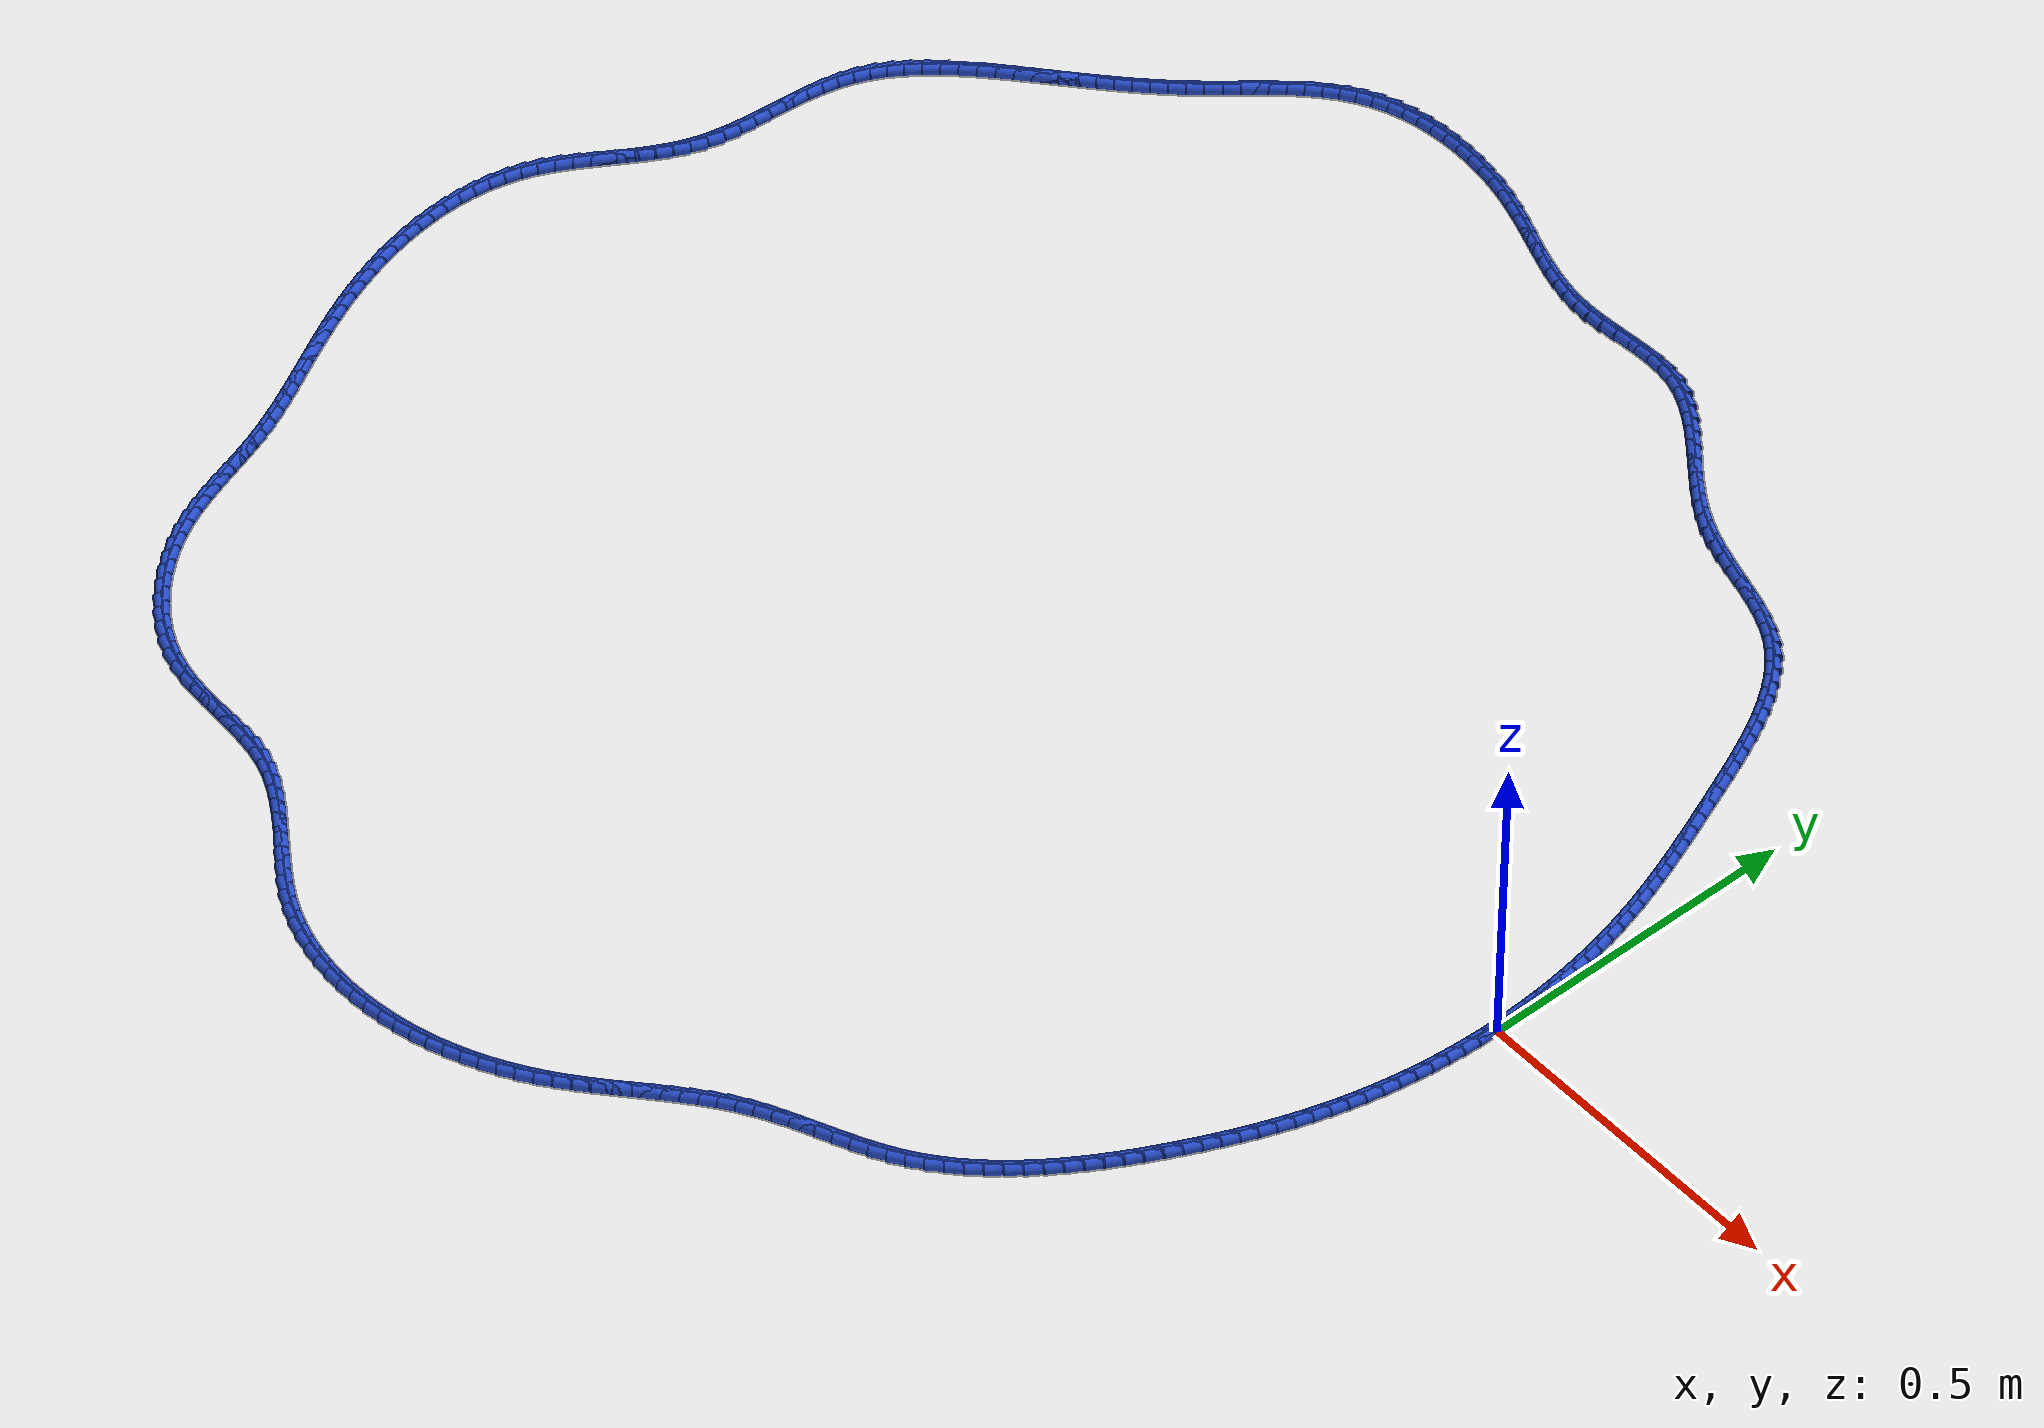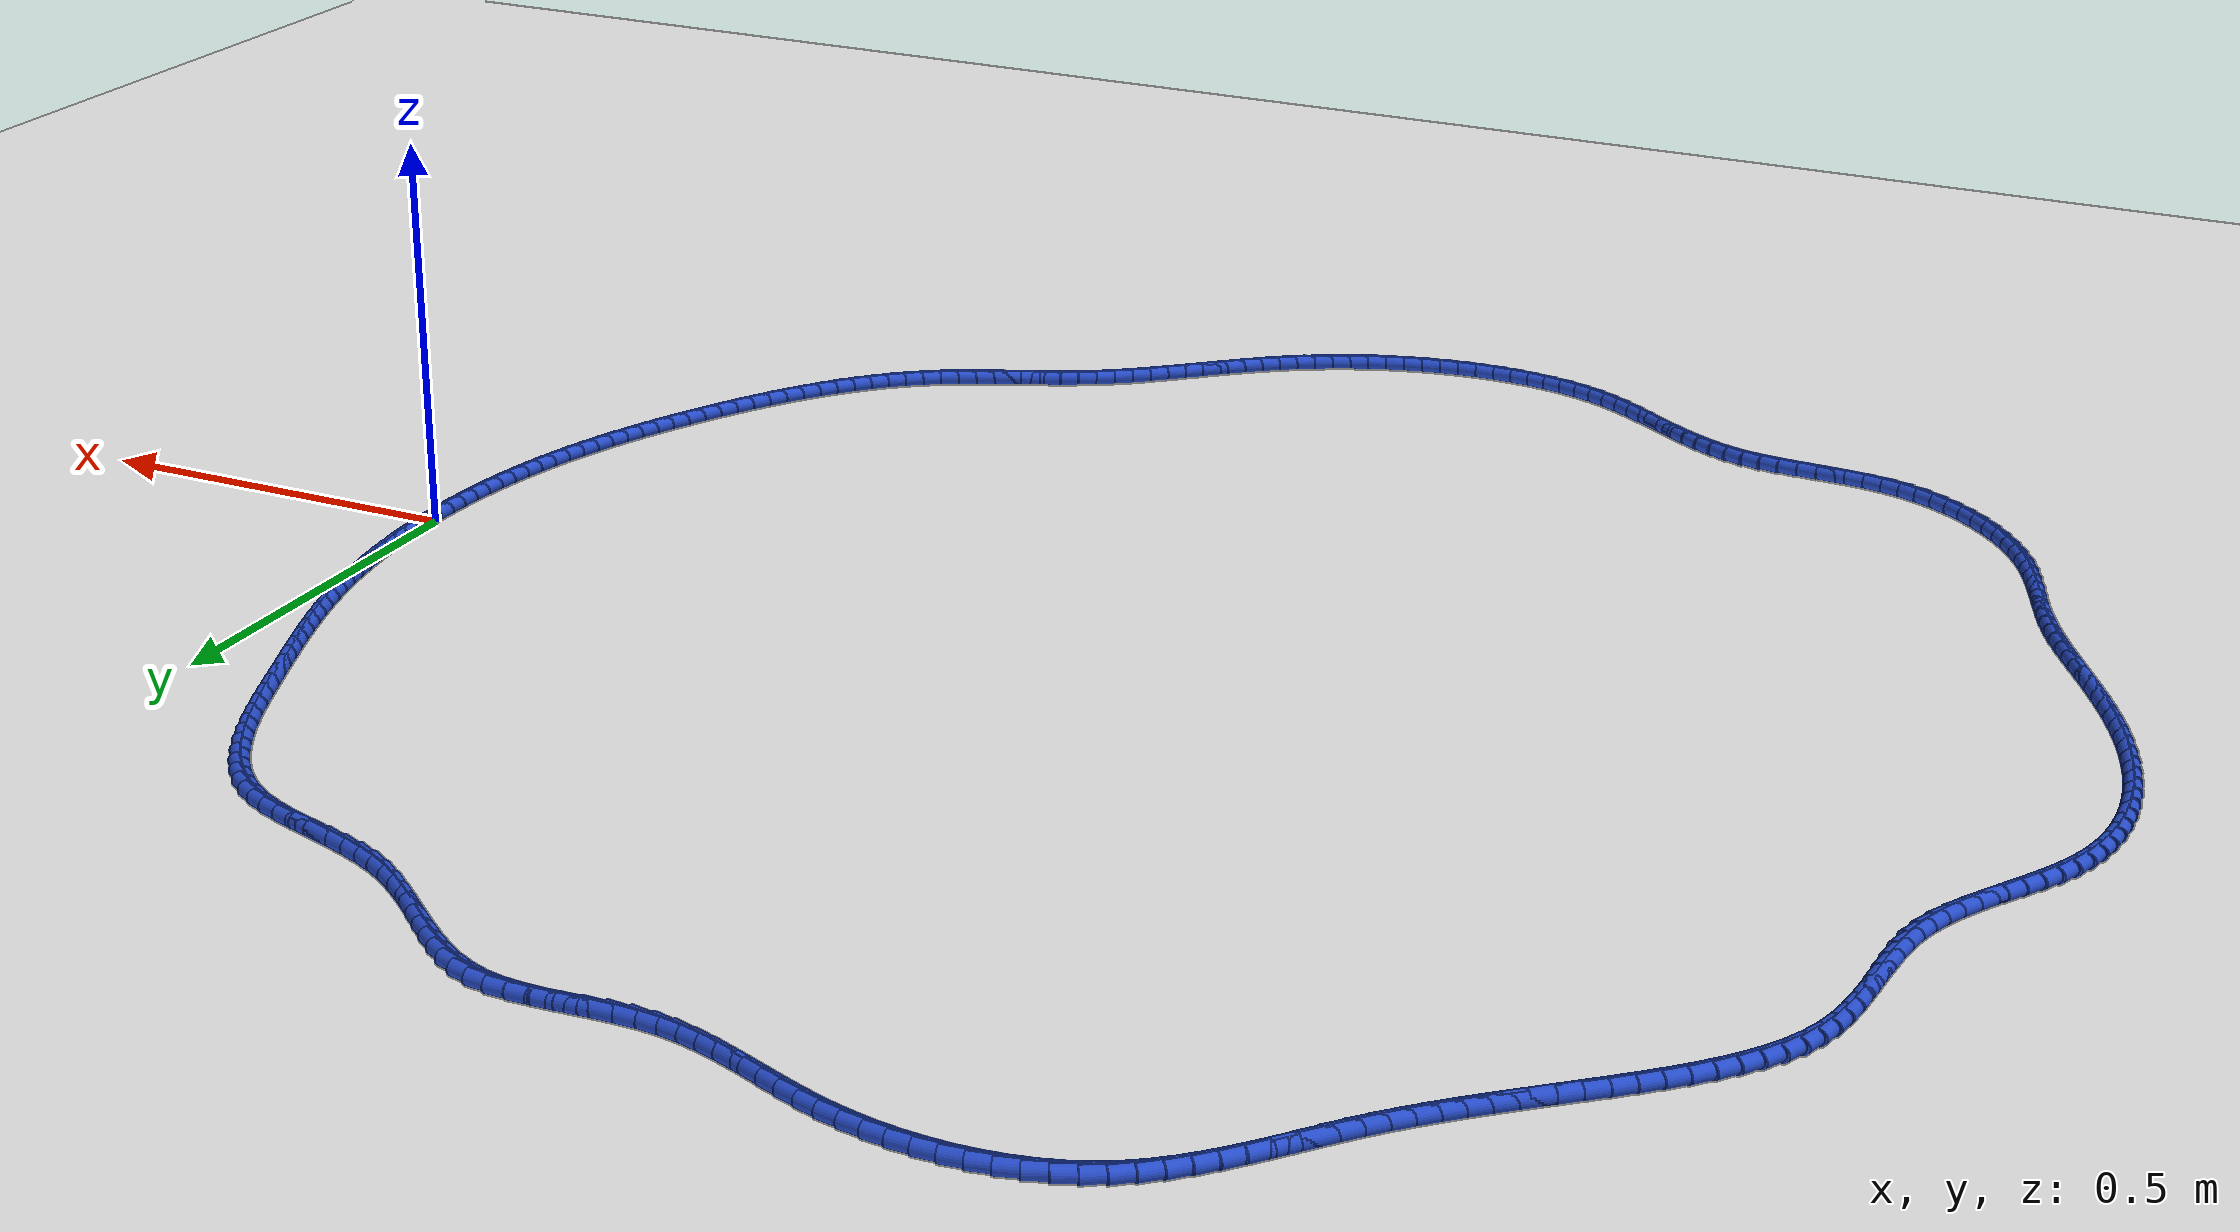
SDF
<sdf version="1.6">
 <world name="default">
  <light name="sun" type="directional">
   <pose>0 0 10 0 -0 0</pose>
   <diffuse>0.8 0.8 0.8 1</diffuse>
   <specular>0.2 0.2 0.2 1</specular>
   <attenuation>
    <range>1000</range>
    <constant>0.9</constant>
    <linear>0.01</linear>
    <quadratic>0.001</quadratic>
   </attenuation>
   <direction>-0.5 0.1 -0.9</direction>
  </light>
  <model name="ground_plane">
   <static>1</static>
   <link name="link">
    <collision name="collision">
     <geometry><plane><normal>0 0 1</normal><size>100 100</size></plane></geometry>
     <surface><friction><ode><mu>100</mu><mu2>50</mu2></ode></friction></surface>
    </collision>
    <visual name="visual">
     <cast_shadows>0</cast_shadows>
     <geometry><plane><normal>0 0 1</normal><size>100 100</size></plane></geometry>
     <material>
      <script><uri>file://media/materials/scripts/gazebo.material</uri><name>Gazebo/WhiteGlow</name></script>
     </material>
    </visual>
   </link>
  </model>
  <gravity>0 0 -9.8</gravity>
  <magnetic_field>6e-06 2.3e-05 -4.2e-05</magnetic_field>
  <atmosphere type="adiabatic"/>
  <physics name="default_physics" default="0" type="ode">
   <max_step_size>0.001</max_step_size>
   <real_time_factor>1</real_time_factor>
   <real_time_update_rate>1000</real_time_update_rate>
  </physics>
  <scene><ambient>0.4 0.4 0.4 1</ambient><background>0.7 0.7 0.7 1</background><shadows>1</shadows></scene>
  <spherical_coordinates>
   <surface_model>EARTH_WGS84</surface_model>
   <latitude_deg>0</latitude_deg>
   <longitude_deg>0</longitude_deg>
   <elevation>0</elevation>
   <heading_deg>0</heading_deg>
  </spherical_coordinates>
  <model name="line">
   <link name="link_0">
    <pose>-9.107298248878237e-18 2.0816681711721685e-17 0.01 0 1.57 -1.5558239799018678</pose>
    <collision name="collision">
     <geometry><cylinder><radius>0.01</radius><length>0.08</length></cylinder></geometry>
    </collision>
    <visual name="visual">
     <material>
      <script><name>Gazebo/Blue</name><uri>file://media/materials/scripts/gazebo.material</uri></script>
     </material>
     <geometry><cylinder><radius>0.01</radius><length>0.08</length></cylinder></geometry>
    </visual>
   </link>
   <link name="link_1">
    <pose>-0.00038648437528154275 0.02581128383273967 0.01 0 1.57 -1.5303639088603733</pose>
    <collision name="collision">
     <geometry><cylinder><radius>0.01</radius><length>0.08</length></cylinder></geometry>
    </collision>
    <visual name="visual">
     <material>
      <script><name>Gazebo/Blue</name><uri>file://media/materials/scripts/gazebo.material</uri></script>
     </material>
     <geometry><cylinder><radius>0.01</radius><length>0.08</length></cylinder></geometry>
    </visual>
   </link>
   <link name="link_2">
    <pose>-0.0014299562711068393 0.05160502240473621 0.01 0 1.57 -1.5050837420746004</pose>
    <collision name="collision">
     <geometry><cylinder><radius>0.01</radius><length>0.08</length></cylinder></geometry>
    </collision>
    <visual name="visual">
     <material>
      <script><name>Gazebo/Blue</name><uri>file://media/materials/scripts/gazebo.material</uri></script>
     </material>
     <geometry><cylinder><radius>0.01</radius><length>0.08</length></cylinder></geometry>
    </visual>
   </link>
   <link name="link_3">
    <pose>-0.003124192199501283 0.07735041929979825 0.01 0 1.57 -1.4799246754344486</pose>
    <collision name="collision">
     <geometry><cylinder><radius>0.01</radius><length>0.08</length></cylinder></geometry>
    </collision>
    <visual name="visual">
     <material>
      <script><name>Gazebo/Blue</name><uri>file://media/materials/scripts/gazebo.material</uri></script>
     </material>
     <geometry><cylinder><radius>0.01</radius><length>0.08</length></cylinder></geometry>
    </visual>
   </link>
   <link name="link_4">
    <pose>-0.005462968672490262 0.10301667810173439 0.01 0 1.57 -1.4548275573112686</pose>
    <collision name="collision">
     <geometry><cylinder><radius>0.01</radius><length>0.08</length></cylinder></geometry>
    </collision>
    <visual name="visual">
     <material>
      <script><name>Gazebo/Blue</name><uri>file://media/materials/scripts/gazebo.material</uri></script>
     </material>
     <geometry><cylinder><radius>0.01</radius><length>0.08</length></cylinder></geometry>
    </visual>
   </link>
   <link name="link_5">
    <pose>-0.008440062202099165 0.1285730023943533 0.01 0 1.57 -1.4297327066731442</pose>
    <collision name="collision">
     <geometry><cylinder><radius>0.01</radius><length>0.08</length></cylinder></geometry>
    </collision>
    <visual name="visual">
     <material>
      <script><name>Gazebo/Blue</name><uri>file://media/materials/scripts/gazebo.material</uri></script>
     </material>
     <geometry><cylinder><radius>0.01</radius><length>0.08</length></cylinder></geometry>
    </visual>
   </link>
   <link name="link_6">
    <pose>-0.012049249300353372 0.15398859576146345 0.01 0 1.57 -1.4045797138071554</pose>
    <collision name="collision">
     <geometry><cylinder><radius>0.01</radius><length>0.08</length></cylinder></geometry>
    </collision>
    <visual name="visual">
     <material>
      <script><name>Gazebo/Blue</name><uri>file://media/materials/scripts/gazebo.material</uri></script>
     </material>
     <geometry><cylinder><radius>0.01</radius><length>0.08</length></cylinder></geometry>
    </visual>
   </link>
   <link name="link_7">
    <pose>-0.016284306479278275 0.17923266178687358 0.01 0 1.57 -1.3793072278453558</pose>
    <collision name="collision">
     <geometry><cylinder><radius>0.01</radius><length>0.08</length></cylinder></geometry>
    </collision>
    <visual name="visual">
     <material>
      <script><name>Gazebo/Blue</name><uri>file://media/materials/scripts/gazebo.material</uri></script>
     </material>
     <geometry><cylinder><radius>0.01</radius><length>0.08</length></cylinder></geometry>
    </visual>
   </link>
   <link name="link_8">
    <pose>-0.02113901025089926 0.2042744040543923 0.01 0 1.57 -1.3538527353111016</pose>
    <collision name="collision">
     <geometry><cylinder><radius>0.01</radius><length>0.08</length></cylinder></geometry>
    </collision>
    <visual name="visual">
     <material>
      <script><name>Gazebo/Blue</name><uri>file://media/materials/scripts/gazebo.material</uri></script>
     </material>
     <geometry><cylinder><radius>0.01</radius><length>0.08</length></cylinder></geometry>
    </visual>
   </link>
   <link name="link_9">
    <pose>-0.026607137127241706 0.229083026147828 0.01 0 1.57 -1.3282246430951223</pose>
    <collision name="collision">
     <geometry><cylinder><radius>0.01</radius><length>0.08</length></cylinder></geometry>
    </collision>
    <visual name="visual">
     <material>
      <script><name>Gazebo/Blue</name><uri>file://media/materials/scripts/gazebo.material</uri></script>
     </material>
     <geometry><cylinder><radius>0.01</radius><length>0.08</length></cylinder></geometry>
    </visual>
   </link>
   <link name="link_10">
    <pose>-0.032681290280303234 0.2536306016432154 0.01 0 1.57 -1.303562085500761</pose>
    <collision name="collision">
     <geometry><cylinder><radius>0.01</radius><length>0.08</length></cylinder></geometry>
    </collision>
    <visual name="visual">
     <material>
      <script><name>Gazebo/Blue</name><uri>file://media/materials/scripts/gazebo.material</uri></script>
     </material>
     <geometry><cylinder><radius>0.01</radius><length>0.08</length></cylinder></geometry>
    </visual>
   </link>
   <link name="link_11">
    <pose>-0.03933538994244768 0.2779349026270228 0.01 0 1.57 -1.2809246756482058</pose>
    <collision name="collision">
     <geometry><cylinder><radius>0.01</radius><length>0.08</length></cylinder></geometry>
    </collision>
    <visual name="visual">
     <material>
      <script><name>Gazebo/Blue</name><uri>file://media/materials/scripts/gazebo.material</uri></script>
     </material>
     <geometry><cylinder><radius>0.01</radius><length>0.08</length></cylinder></geometry>
    </visual>
   </link>
   <link name="link_12">
    <pose>-0.04652837545611567 0.3020503444746176 0.01 0 1.57 -1.2604830216874552</pose>
    <collision name="collision">
     <geometry><cylinder><radius>0.01</radius><length>0.08</length></cylinder></geometry>
    </collision>
    <visual name="visual">
     <material>
      <script><name>Gazebo/Blue</name><uri>file://media/materials/scripts/gazebo.material</uri></script>
     </material>
     <geometry><cylinder><radius>0.01</radius><length>0.08</length></cylinder></geometry>
    </visual>
   </link>
   <link name="link_13">
    <pose>-0.05421876457126814 0.32603237377747685 0.01 0 1.57 -1.24234817541048</pose>
    <collision name="collision">
     <geometry><cylinder><radius>0.01</radius><length>0.08</length></cylinder></geometry>
    </collision>
    <visual name="visual">
     <material>
      <script><name>Gazebo/Blue</name><uri>file://media/materials/scripts/gazebo.material</uri></script>
     </material>
     <geometry><cylinder><radius>0.01</radius><length>0.08</length></cylinder></geometry>
    </visual>
   </link>
   <link name="link_14">
    <pose>-0.06236507503786607 0.3499364371270776 0.01 0 1.57 -1.2265983727121146</pose>
    <collision name="collision">
     <geometry><cylinder><radius>0.01</radius><length>0.08</length></cylinder></geometry>
    </collision>
    <visual name="visual">
     <material>
      <script><name>Gazebo/Blue</name><uri>file://media/materials/scripts/gazebo.material</uri></script>
     </material>
     <geometry><cylinder><radius>0.01</radius><length>0.08</length></cylinder></geometry>
    </visual>
   </link>
   <link name="link_15">
    <pose>-0.07092582460587038 0.3738179811148969 0.01 0 1.57 -1.213280773242131</pose>
    <collision name="collision">
     <geometry><cylinder><radius>0.01</radius><length>0.08</length></cylinder></geometry>
    </collision>
    <visual name="visual">
     <material>
      <script><name>Gazebo/Blue</name><uri>file://media/materials/scripts/gazebo.material</uri></script>
     </material>
     <geometry><cylinder><radius>0.01</radius><length>0.08</length></cylinder></geometry>
    </visual>
   </link>
   <link name="link_16">
    <pose>-0.07985953102524208 0.39773245233241206 0.01 0 1.57 -1.2024138637460513</pose>
    <collision name="collision">
     <geometry><cylinder><radius>0.01</radius><length>0.08</length></cylinder></geometry>
    </collision>
    <visual name="visual">
     <material>
      <script><name>Gazebo/Blue</name><uri>file://media/materials/scripts/gazebo.material</uri></script>
     </material>
     <geometry><cylinder><radius>0.01</radius><length>0.08</length></cylinder></geometry>
    </visual>
   </link>
   <link name="link_17">
    <pose>-0.0891247120459421 0.42173529737109994 0.01 0 1.57 -1.1939902363397423</pose>
    <collision name="collision">
     <geometry><cylinder><radius>0.01</radius><length>0.08</length></cylinder></geometry>
    </collision>
    <visual name="visual">
     <material>
      <script><name>Gazebo/Blue</name><uri>file://media/materials/scripts/gazebo.material</uri></script>
     </material>
     <geometry><cylinder><radius>0.01</radius><length>0.08</length></cylinder></geometry>
    </visual>
   </link>
   <link name="link_18">
    <pose>-0.09867988541793139 0.44588196282243764 0.01 0 1.57 -1.1879795015572436</pose>
    <collision name="collision">
     <geometry><cylinder><radius>0.01</radius><length>0.08</length></cylinder></geometry>
    </collision>
    <visual name="visual">
     <material>
      <script><name>Gazebo/Blue</name><uri>file://media/materials/scripts/gazebo.material</uri></script>
     </material>
     <geometry><cylinder><radius>0.01</radius><length>0.08</length></cylinder></geometry>
    </visual>
   </link>
   <link name="link_19">
    <pose>-0.10848356889117092 0.47022789527790226 0.01 0 1.57 -1.1843311557571234</pose>
    <collision name="collision">
     <geometry><cylinder><radius>0.01</radius><length>0.08</length></cylinder></geometry>
    </collision>
    <visual name="visual">
     <material>
      <script><name>Gazebo/Blue</name><uri>file://media/materials/scripts/gazebo.material</uri></script>
     </material>
     <geometry><cylinder><radius>0.01</radius><length>0.08</length></cylinder></geometry>
    </visual>
   </link>
   <link name="link_20">
    <pose>-0.11849428021562163 0.494828541328971 0.01 0 1.57 -1.1823245672838831</pose>
    <collision name="collision">
     <geometry><cylinder><radius>0.01</radius><length>0.08</length></cylinder></geometry>
    </collision>
    <visual name="visual">
     <material>
      <script><name>Gazebo/Blue</name><uri>file://media/materials/scripts/gazebo.material</uri></script>
     </material>
     <geometry><cylinder><radius>0.01</radius><length>0.08</length></cylinder></geometry>
    </visual>
   </link>
   <link name="link_21">
    <pose>-0.12868170892180247 0.5197202737119428 0.01 0 1.57 -1.1761671465852923</pose>
    <collision name="collision">
     <geometry><cylinder><radius>0.01</radius><length>0.08</length></cylinder></geometry>
    </collision>
    <visual name="visual">
     <material>
      <script><name>Gazebo/Blue</name><uri>file://media/materials/scripts/gazebo.material</uri></script>
     </material>
     <geometry><cylinder><radius>0.01</radius><length>0.08</length></cylinder></geometry>
    </visual>
   </link>
   <link name="link_22">
    <pose>-0.13911452883023867 0.5447704668550407 0.01 0 1.57 -1.1628799807247618</pose>
    <collision name="collision">
     <geometry><cylinder><radius>0.01</radius><length>0.08</length></cylinder></geometry>
    </collision>
    <visual name="visual">
     <material>
      <script><name>Gazebo/Blue</name><uri>file://media/materials/scripts/gazebo.material</uri></script>
     </material>
     <geometry><cylinder><radius>0.01</radius><length>0.08</length></cylinder></geometry>
    </visual>
   </link>
   <link name="link_23">
    <pose>-0.14991313088695515 0.5697581972686315 0.01 0 1.57 -1.142280752724943</pose>
    <collision name="collision">
     <geometry><cylinder><radius>0.01</radius><length>0.08</length></cylinder></geometry>
    </collision>
    <visual name="visual">
     <material>
      <script><name>Gazebo/Blue</name><uri>file://media/materials/scripts/gazebo.material</uri></script>
     </material>
     <geometry><cylinder><radius>0.01</radius><length>0.08</length></cylinder></geometry>
    </visual>
   </link>
   <link name="link_24">
    <pose>-0.16119835637123747 0.5944617725980527 0.01 0 1.57 -1.113988222840046</pose>
    <collision name="collision">
     <geometry><cylinder><radius>0.01</radius><length>0.08</length></cylinder></geometry>
    </collision>
    <visual name="visual">
     <material>
      <script><name>Gazebo/Blue</name><uri>file://media/materials/scripts/gazebo.material</uri></script>
     </material>
     <geometry><cylinder><radius>0.01</radius><length>0.08</length></cylinder></geometry>
    </visual>
   </link>
   <link name="link_25">
    <pose>-0.17309104656237134 0.6186595004886406 0.01 0 1.57 -1.0774099486632638</pose>
    <collision name="collision">
     <geometry><cylinder><radius>0.01</radius><length>0.08</length></cylinder></geometry>
    </collision>
    <visual name="visual">
     <material>
      <script><name>Gazebo/Blue</name><uri>file://media/materials/scripts/gazebo.material</uri></script>
     </material>
     <geometry><cylinder><radius>0.01</radius><length>0.08</length></cylinder></geometry>
    </visual>
   </link>
   <link name="link_26">
    <pose>-0.18571204273964248 0.6421296885857328 0.01 0 1.57 -1.031763293250655</pose>
    <collision name="collision">
     <geometry><cylinder><radius>0.01</radius><length>0.08</length></cylinder></geometry>
    </collision>
    <visual name="visual">
     <material>
      <script><name>Gazebo/Blue</name><uri>file://media/materials/scripts/gazebo.material</uri></script>
     </material>
     <geometry><cylinder><radius>0.01</radius><length>0.08</length></cylinder></geometry>
    </visual>
   </link>
   <link name="link_27">
    <pose>-0.19918218618233643 0.6646506445346656 0.01 0 1.57 -0.9761185756669005</pose>
    <collision name="collision">
     <geometry><cylinder><radius>0.01</radius><length>0.08</length></cylinder></geometry>
    </collision>
    <visual name="visual">
     <material>
      <script><name>Gazebo/Blue</name><uri>file://media/materials/scripts/gazebo.material</uri></script>
     </material>
     <geometry><cylinder><radius>0.01</radius><length>0.08</length></cylinder></geometry>
    </visual>
   </link>
   <link name="link_28">
    <pose>-0.21362231816973884 0.6860006759807761 0.01 0 1.57 -0.9094869585952983</pose>
    <collision name="collision">
     <geometry><cylinder><radius>0.01</radius><length>0.08</length></cylinder></geometry>
    </collision>
    <visual name="visual">
     <material>
      <script><name>Gazebo/Blue</name><uri>file://media/materials/scripts/gazebo.material</uri></script>
     </material>
     <geometry><cylinder><radius>0.01</radius><length>0.08</length></cylinder></geometry>
    </visual>
   </link>
   <link name="link_29">
    <pose>-0.22915327998113538 0.7059580905694012 0.01 0 1.57 -0.8309826037865946</pose>
    <collision name="collision">
     <geometry><cylinder><radius>0.01</radius><length>0.08</length></cylinder></geometry>
    </collision>
    <visual name="visual">
     <material>
      <script><name>Gazebo/Blue</name><uri>file://media/materials/scripts/gazebo.material</uri></script>
     </material>
     <geometry><cylinder><radius>0.01</radius><length>0.08</length></cylinder></geometry>
    </visual>
   </link>
   <link name="link_30">
    <pose>-0.24589591289581172 0.7243011959458776 0.01 0 1.57 -0.7400868185193471</pose>
    <collision name="collision">
     <geometry><cylinder><radius>0.01</radius><length>0.08</length></cylinder></geometry>
    </collision>
    <visual name="visual">
     <material>
      <script><name>Gazebo/Blue</name><uri>file://media/materials/scripts/gazebo.material</uri></script>
     </material>
     <geometry><cylinder><radius>0.01</radius><length>0.08</length></cylinder></geometry>
    </visual>
   </link>
   <link name="link_31">
    <pose>-0.26397105819305355 0.7408082997555427 0.01 0 1.57 -0.6370147606950207</pose>
    <collision name="collision">
     <geometry><cylinder><radius>0.01</radius><length>0.08</length></cylinder></geometry>
    </collision>
    <visual name="visual">
     <material>
      <script><name>Gazebo/Blue</name><uri>file://media/materials/scripts/gazebo.material</uri></script>
     </material>
     <geometry><cylinder><radius>0.01</radius><length>0.08</length></cylinder></geometry>
    </visual>
   </link>
   <link name="link_32">
    <pose>-0.2834995571521465 0.755257709643733 0.01 0 1.57 -0.5255721786639235</pose>
    <collision name="collision">
     <geometry><cylinder><radius>0.01</radius><length>0.08</length></cylinder></geometry>
    </collision>
    <visual name="visual">
     <material>
      <script><name>Gazebo/Blue</name><uri>file://media/materials/scripts/gazebo.material</uri></script>
     </material>
     <geometry><cylinder><radius>0.01</radius><length>0.08</length></cylinder></geometry>
    </visual>
   </link>
   <link name="link_33">
    <pose>-0.3045726057084721 0.7674797507098817 0.01 0 1.57 -0.4290555227034722</pose>
    <collision name="collision">
     <geometry><cylinder><radius>0.01</radius><length>0.08</length></cylinder></geometry>
    </collision>
    <visual name="visual">
     <material>
      <script><name>Gazebo/Blue</name><uri>file://media/materials/scripts/gazebo.material</uri></script>
     </material>
     <geometry><cylinder><radius>0.01</radius><length>0.08</length></cylinder></geometry>
    </visual>
   </link>
   <link name="link_34">
    <pose>-0.32702653983433433 0.7777519402490459 0.01 0 1.57 -0.3587634826626513</pose>
    <collision name="collision">
     <geometry><cylinder><radius>0.01</radius><length>0.08</length></cylinder></geometry>
    </collision>
    <visual name="visual">
     <material>
      <script><name>Gazebo/Blue</name><uri>file://media/materials/scripts/gazebo.material</uri></script>
     </material>
     <geometry><cylinder><radius>0.01</radius><length>0.08</length></cylinder></geometry>
    </visual>
   </link>
   <link name="link_35">
    <pose>-0.3505677990555753 0.7865797194576891 0.01 0 1.57 -0.31356564099690865</pose>
    <collision name="collision">
     <geometry><cylinder><radius>0.01</radius><length>0.08</length></cylinder></geometry>
    </collision>
    <visual name="visual">
     <material>
      <script><name>Gazebo/Blue</name><uri>file://media/materials/scripts/gazebo.material</uri></script>
     </material>
     <geometry><cylinder><radius>0.01</radius><length>0.08</length></cylinder></geometry>
    </visual>
   </link>
   <link name="link_36">
    <pose>-0.37490178841728555 0.7944703446926963 0.01 0 1.57 -0.29186647726337633</pose>
    <collision name="collision">
     <geometry><cylinder><radius>0.01</radius><length>0.08</length></cylinder></geometry>
    </collision>
    <visual name="visual">
     <material>
      <script><name>Gazebo/Blue</name><uri>file://media/materials/scripts/gazebo.material</uri></script>
     </material>
     <geometry><cylinder><radius>0.01</radius><length>0.08</length></cylinder></geometry>
    </visual>
   </link>
   <link name="link_37">
    <pose>-0.39973391296455635 0.8019310723109544 0.01 0 1.57 -0.29246008512684474</pose>
    <collision name="collision">
     <geometry><cylinder><radius>0.01</radius><length>0.08</length></cylinder></geometry>
    </collision>
    <visual name="visual">
     <material>
      <script><name>Gazebo/Blue</name><uri>file://media/materials/scripts/gazebo.material</uri></script>
     </material>
     <geometry><cylinder><radius>0.01</radius><length>0.08</length></cylinder></geometry>
    </visual>
   </link>
   <link name="link_38">
    <pose>-0.4247695777424789 0.8094691586693493 0.01 0 1.57 -0.3148011750580302</pose>
    <collision name="collision">
     <geometry><cylinder><radius>0.01</radius><length>0.08</length></cylinder></geometry>
    </collision>
    <visual name="visual">
     <material>
      <script><name>Gazebo/Blue</name><uri>file://media/materials/scripts/gazebo.material</uri></script>
     </material>
     <geometry><cylinder><radius>0.01</radius><length>0.08</length></cylinder></geometry>
    </visual>
   </link>
   <link name="link_39">
    <pose>-0.4497141877961438 0.8175918601247669 0.01 0 1.57 -0.35894782074927645</pose>
    <collision name="collision">
     <geometry><cylinder><radius>0.01</radius><length>0.08</length></cylinder></geometry>
    </collision>
    <visual name="visual">
     <material>
      <script><name>Gazebo/Blue</name><uri>file://media/materials/scripts/gazebo.material</uri></script>
     </material>
     <geometry><cylinder><radius>0.01</radius><length>0.08</length></cylinder></geometry>
    </visual>
   </link>
   <link name="link_40">
    <pose>-0.4742731481706419 0.8268064330340932 0.01 0 1.57 -0.42522925370393405</pose>
    <collision name="collision">
     <geometry><cylinder><radius>0.01</radius><length>0.08</length></cylinder></geometry>
    </collision>
    <visual name="visual">
     <material>
      <script><name>Gazebo/Blue</name><uri>file://media/materials/scripts/gazebo.material</uri></script>
     </material>
     <geometry><cylinder><radius>0.01</radius><length>0.08</length></cylinder></geometry>
    </visual>
   </link>
   <link name="link_41">
    <pose>-0.49815186391106436 0.8376201337542142 0.01 0 1.57 -0.5094535954138438</pose>
    <collision name="collision">
     <geometry><cylinder><radius>0.01</radius><length>0.08</length></cylinder></geometry>
    </collision>
    <visual name="visual">
     <material>
      <script><name>Gazebo/Blue</name><uri>file://media/materials/scripts/gazebo.material</uri></script>
     </material>
     <geometry><cylinder><radius>0.01</radius><length>0.08</length></cylinder></geometry>
    </visual>
   </link>
   <link name="link_42">
    <pose>-0.5211029759396922 0.8504415790092729 0.01 0 1.57 -0.5836437808994529</pose>
    <collision name="collision">
     <geometry><cylinder><radius>0.01</radius><length>0.08</length></cylinder></geometry>
    </collision>
    <visual name="visual">
     <material>
      <script><name>Gazebo/Blue</name><uri>file://media/materials/scripts/gazebo.material</uri></script>
     </material>
     <geometry><cylinder><radius>0.01</radius><length>0.08</length></cylinder></geometry>
    </visual>
   </link>
   <link name="link_43">
    <pose>-0.5431909472179036 0.8650282276906818 0.01 0 1.57 -0.637002494441879</pose>
    <collision name="collision">
     <geometry><cylinder><radius>0.01</radius><length>0.08</length></cylinder></geometry>
    </collision>
    <visual name="visual">
     <material>
      <script><name>Gazebo/Blue</name><uri>file://media/materials/scripts/gazebo.material</uri></script>
     </material>
     <geometry><cylinder><radius>0.01</radius><length>0.08</length></cylinder></geometry>
    </visual>
   </link>
   <link name="link_44">
    <pose>-0.5646066382283363 0.8808735909065486 0.01 0 1.57 -0.6703311933788669</pose>
    <collision name="collision">
     <geometry><cylinder><radius>0.01</radius><length>0.08</length></cylinder></geometry>
    </collision>
    <visual name="visual">
     <material>
      <script><name>Gazebo/Blue</name><uri>file://media/materials/scripts/gazebo.material</uri></script>
     </material>
     <geometry><cylinder><radius>0.01</radius><length>0.08</length></cylinder></geometry>
    </visual>
   </link>
   <link name="link_45">
    <pose>-0.5855412694065132 0.8974704280986114 0.01 0 1.57 -0.6842734671761392</pose>
    <collision name="collision">
     <geometry><cylinder><radius>0.01</radius><length>0.08</length></cylinder></geometry>
    </collision>
    <visual name="visual">
     <material>
      <script><name>Gazebo/Blue</name><uri>file://media/materials/scripts/gazebo.material</uri></script>
     </material>
     <geometry><cylinder><radius>0.01</radius><length>0.08</length></cylinder></geometry>
    </visual>
   </link>
   <link name="link_46">
    <pose>-0.6061860611879569 0.9143114987086075 0.01 0 1.57 -0.6789151551553769</pose>
    <collision name="collision">
     <geometry><cylinder><radius>0.01</radius><length>0.08</length></cylinder></geometry>
    </collision>
    <visual name="visual">
     <material>
      <script><name>Gazebo/Blue</name><uri>file://media/materials/scripts/gazebo.material</uri></script>
     </material>
     <geometry><cylinder><radius>0.01</radius><length>0.08</length></cylinder></geometry>
    </visual>
   </link>
   <link name="link_47">
    <pose>-0.6267322340081901 0.9308895621782742 0.01 0 1.57 -0.6536173579724586</pose>
    <collision name="collision">
     <geometry><cylinder><radius>0.01</radius><length>0.08</length></cylinder></geometry>
    </collision>
    <visual name="visual">
     <material>
      <script><name>Gazebo/Blue</name><uri>file://media/materials/scripts/gazebo.material</uri></script>
     </material>
     <geometry><cylinder><radius>0.01</radius><length>0.08</length></cylinder></geometry>
    </visual>
   </link>
   <link name="link_48">
    <pose>-0.6473710083027352 0.9466973779493486 0.01 0 1.57 -0.6070117447316465</pose>
    <collision name="collision">
     <geometry><cylinder><radius>0.01</radius><length>0.08</length></cylinder></geometry>
    </collision>
    <visual name="visual">
     <material>
      <script><name>Gazebo/Blue</name><uri>file://media/materials/scripts/gazebo.material</uri></script>
     </material>
     <geometry><cylinder><radius>0.01</radius><length>0.08</length></cylinder></geometry>
    </visual>
   </link>
   <link name="link_49">
    <pose>-0.6682936045071151 0.9612277054635684 0.01 0 1.57 -0.537218118958133</pose>
    <collision name="collision">
     <geometry><cylinder><radius>0.01</radius><length>0.08</length></cylinder></geometry>
    </collision>
    <visual name="visual">
     <material>
      <script><name>Gazebo/Blue</name><uri>file://media/materials/scripts/gazebo.material</uri></script>
     </material>
     <geometry><cylinder><radius>0.01</radius><length>0.08</length></cylinder></geometry>
    </visual>
   </link>
   <link name="link_50">
    <pose>-0.6896912430568524 0.9739733041626711 0.01 0 1.57 -0.44245964181043396</pose>
    <collision name="collision">
     <geometry><cylinder><radius>0.01</radius><length>0.08</length></cylinder></geometry>
    </collision>
    <visual name="visual">
     <material>
      <script><name>Gazebo/Blue</name><uri>file://media/materials/scripts/gazebo.material</uri></script>
     </material>
     <geometry><cylinder><radius>0.01</radius><length>0.08</length></cylinder></geometry>
    </visual>
   </link>
   <link name="link_51">
    <pose>-0.7117551443874699 0.984426933488394 0.01 0 1.57 -0.3222985053641382</pose>
    <collision name="collision">
     <geometry><cylinder><radius>0.01</radius><length>0.08</length></cylinder></geometry>
    </collision>
    <visual name="visual">
     <material>
      <script><name>Gazebo/Blue</name><uri>file://media/materials/scripts/gazebo.material</uri></script>
     </material>
     <geometry><cylinder><radius>0.01</radius><length>0.08</length></cylinder></geometry>
    </visual>
   </link>
   <link name="link_52">
    <pose>-0.7346765289344896 0.992081352882474 0.01 0 1.57 -0.18304156253018988</pose>
    <collision name="collision">
     <geometry><cylinder><radius>0.01</radius><length>0.08</length></cylinder></geometry>
    </collision>
    <visual name="visual">
     <material>
      <script><name>Gazebo/Blue</name><uri>file://media/materials/scripts/gazebo.material</uri></script>
     </material>
     <geometry><cylinder><radius>0.01</radius><length>0.08</length></cylinder></geometry>
    </visual>
   </link>
   <link name="link_53">
    <pose>-0.7586194103235463 0.996513504806401 0.01 0 1.57 -0.06379458460760433</pose>
    <collision name="collision">
     <geometry><cylinder><radius>0.01</radius><length>0.08</length></cylinder></geometry>
    </collision>
    <visual name="visual">
     <material>
      <script><name>Gazebo/Blue</name><uri>file://media/materials/scripts/gazebo.material</uri></script>
     </material>
     <geometry><cylinder><radius>0.01</radius><length>0.08</length></cylinder></geometry>
    </visual>
   </link>
   <link name="link_54">
    <pose>-0.783488654509642 0.9981021836684696 0.01 0 1.57 0.01689655816658638</pose>
    <collision name="collision">
     <geometry><cylinder><radius>0.01</radius><length>0.08</length></cylinder></geometry>
    </collision>
    <visual name="visual">
     <material>
      <script><name>Gazebo/Blue</name><uri>file://media/materials/scripts/gazebo.material</uri></script>
     </material>
     <geometry><cylinder><radius>0.01</radius><length>0.08</length></cylinder></geometry>
    </visual>
   </link>
   <link name="link_55">
    <pose>-0.8090455892162448 0.9976703183355835 0.01 0 1.57 0.06239927145488688</pose>
    <collision name="collision">
     <geometry><cylinder><radius>0.01</radius><length>0.08</length></cylinder></geometry>
    </collision>
    <visual name="visual">
     <material>
      <script><name>Gazebo/Blue</name><uri>file://media/materials/scripts/gazebo.material</uri></script>
     </material>
     <geometry><cylinder><radius>0.01</radius><length>0.08</length></cylinder></geometry>
    </visual>
   </link>
   <link name="link_56">
    <pose>-0.835050018701258 0.996045551565482 0.01 0 1.57 0.07577581530114758</pose>
    <collision name="collision">
     <geometry><cylinder><radius>0.01</radius><length>0.08</length></cylinder></geometry>
    </collision>
    <visual name="visual">
     <material>
      <script><name>Gazebo/Blue</name><uri>file://media/materials/scripts/gazebo.material</uri></script>
     </material>
     <geometry><cylinder><radius>0.01</radius><length>0.08</length></cylinder></geometry>
    </visual>
   </link>
   <link name="link_57">
    <pose>-0.8612617472225845 0.9940555261159052 0.01 0 1.57 0.05828796879458267</pose>
    <collision name="collision">
     <geometry><cylinder><radius>0.01</radius><length>0.08</length></cylinder></geometry>
    </collision>
    <visual name="visual">
     <material>
      <script><name>Gazebo/Blue</name><uri>file://media/materials/scripts/gazebo.material</uri></script>
     </material>
     <geometry><cylinder><radius>0.01</radius><length>0.08</length></cylinder></geometry>
    </visual>
   </link>
   <link name="link_58">
    <pose>-0.887440579038127 0.992527884744592 0.01 0 1.57 0.009172016622314188</pose>
    <collision name="collision">
     <geometry><cylinder><radius>0.01</radius><length>0.08</length></cylinder></geometry>
    </collision>
    <visual name="visual">
     <material>
      <script><name>Gazebo/Blue</name><uri>file://media/materials/scripts/gazebo.material</uri></script>
     </material>
     <geometry><cylinder><radius>0.01</radius><length>0.08</length></cylinder></geometry>
    </visual>
   </link>
   <link name="link_59">
    <pose>-0.913346318405789 0.9922902702092831 0.01 0 1.57 -0.07218420985978058</pose>
    <collision name="collision">
     <geometry><cylinder><radius>0.01</radius><length>0.08</length></cylinder></geometry>
    </collision>
    <visual name="visual">
     <material>
      <script><name>Gazebo/Blue</name><uri>file://media/materials/scripts/gazebo.material</uri></script>
     </material>
     <geometry><cylinder><radius>0.01</radius><length>0.08</length></cylinder></geometry>
    </visual>
   </link>
   <link name="link_60">
    <pose>-0.938751846424488 0.9941273400051889 0.01 0 1.57 -0.1609225297054341</pose>
    <collision name="collision">
     <geometry><cylinder><radius>0.01</radius><length>0.08</length></cylinder></geometry>
    </collision>
    <visual name="visual">
     <material>
      <script><name>Gazebo/Blue</name><uri>file://media/materials/scripts/gazebo.material</uri></script>
     </material>
     <geometry><cylinder><radius>0.01</radius><length>0.08</length></cylinder></geometry>
    </visual>
   </link>
   <link name="link_61">
    <pose>-0.963630219173782 0.9981657506558663 0.01 0 1.57 -0.23464959813051267</pose>
    <collision name="collision">
     <geometry><cylinder><radius>0.01</radius><length>0.08</length></cylinder></geometry>
    </collision>
    <visual name="visual">
     <material>
      <script><name>Gazebo/Blue</name><uri>file://media/materials/scripts/gazebo.material</uri></script>
     </material>
     <geometry><cylinder><radius>0.01</radius><length>0.08</length></cylinder></geometry>
    </visual>
   </link>
   <link name="link_62">
    <pose>-0.9881109257917644 1.0040179430511984 0.01 0 1.57 -0.29144651557372064</pose>
    <collision name="collision">
     <geometry><cylinder><radius>0.01</radius><length>0.08</length></cylinder></geometry>
    </collision>
    <visual name="visual">
     <material>
      <script><name>Gazebo/Blue</name><uri>file://media/materials/scripts/gazebo.material</uri></script>
     </material>
     <geometry><cylinder><radius>0.01</radius><length>0.08</length></cylinder></geometry>
    </visual>
   </link>
   <link name="link_63">
    <pose>-1.0123276168129538 1.011282679034452 0.01 0 1.57 -0.33096117250889795</pose>
    <collision name="collision">
     <geometry><cylinder><radius>0.01</radius><length>0.08</length></cylinder></geometry>
    </collision>
    <visual name="visual">
     <material>
      <script><name>Gazebo/Blue</name><uri>file://media/materials/scripts/gazebo.material</uri></script>
     </material>
     <geometry><cylinder><radius>0.01</radius><length>0.08</length></cylinder></geometry>
    </visual>
   </link>
   <link name="link_64">
    <pose>-1.0364139427718684 1.0195587204488943 0.01 0 1.57 -0.3533919706312554</pose>
    <collision name="collision">
     <geometry><cylinder><radius>0.01</radius><length>0.08</length></cylinder></geometry>
    </collision>
    <visual name="visual">
     <material>
      <script><name>Gazebo/Blue</name><uri>file://media/materials/scripts/gazebo.material</uri></script>
     </material>
     <geometry><cylinder><radius>0.01</radius><length>0.08</length></cylinder></geometry>
    </visual>
   </link>
   <link name="link_65">
    <pose>-1.0605035542030268 1.0284448291377906 0.01 0 1.57 -0.35913186949999143</pose>
    <collision name="collision">
     <geometry><cylinder><radius>0.01</radius><length>0.08</length></cylinder></geometry>
    </collision>
    <visual name="visual">
     <material>
      <script><name>Gazebo/Blue</name><uri>file://media/materials/scripts/gazebo.material</uri></script>
     </material>
     <geometry><cylinder><radius>0.01</radius><length>0.08</length></cylinder></geometry>
    </visual>
   </link>
   <link name="link_66">
    <pose>-1.0847301016409483 1.037539766944409 0.01 0 1.57 -0.3485719746302068</pose>
    <collision name="collision">
     <geometry><cylinder><radius>0.01</radius><length>0.08</length></cylinder></geometry>
    </collision>
    <visual name="visual">
     <material>
      <script><name>Gazebo/Blue</name><uri>file://media/materials/scripts/gazebo.material</uri></script>
     </material>
     <geometry><cylinder><radius>0.01</radius><length>0.08</length></cylinder></geometry>
    </visual>
   </link>
   <link name="link_67">
    <pose>-1.1092272356201514 1.046442295712016 0.01 0 1.57 -0.32205500865566006</pose>
    <collision name="collision">
     <geometry><cylinder><radius>0.01</radius><length>0.08</length></cylinder></geometry>
    </collision>
    <visual name="visual">
     <material>
      <script><name>Gazebo/Blue</name><uri>file://media/materials/scripts/gazebo.material</uri></script>
     </material>
     <geometry><cylinder><radius>0.01</radius><length>0.08</length></cylinder></geometry>
    </visual>
   </link>
   <link name="link_68">
    <pose>-1.1341286066751541 1.0547511772838778 0.01 0 1.57 -0.2799705867764437</pose>
    <collision name="collision">
     <geometry><cylinder><radius>0.01</radius><length>0.08</length></cylinder></geometry>
    </collision>
    <visual name="visual">
     <material>
      <script><name>Gazebo/Blue</name><uri>file://media/materials/scripts/gazebo.material</uri></script>
     </material>
     <geometry><cylinder><radius>0.01</radius><length>0.08</length></cylinder></geometry>
    </visual>
   </link>
   <link name="link_69">
    <pose>-1.1595675850094735 1.06206545544058 0.01 0 1.57 -0.22673129653218235</pose>
    <collision name="collision">
     <geometry><cylinder><radius>0.01</radius><length>0.08</length></cylinder></geometry>
    </collision>
    <visual name="visual">
     <material>
      <script><name>Gazebo/Blue</name><uri>file://media/materials/scripts/gazebo.material</uri></script>
     </material>
     <geometry><cylinder><radius>0.01</radius><length>0.08</length></cylinder></geometry>
    </visual>
   </link>
   <link name="link_70">
    <pose>-1.1855927819748866 1.0680694184885902 0.01 0 1.57 -0.17150591330955095</pose>
    <collision name="collision">
     <geometry><cylinder><radius>0.01</radius><length>0.08</length></cylinder></geometry>
    </collision>
    <visual name="visual">
     <material>
      <script><name>Gazebo/Blue</name><uri>file://media/materials/scripts/gazebo.material</uri></script>
     </material>
     <geometry><cylinder><radius>0.01</radius><length>0.08</length></cylinder></geometry>
    </visual>
   </link>
   <link name="link_71">
    <pose>-1.2120494218525633 1.0726519072271048 0.01 0 1.57 -0.11483001990689436</pose>
    <collision name="collision">
     <geometry><cylinder><radius>0.01</radius><length>0.08</length></cylinder></geometry>
    </collision>
    <visual name="visual">
     <material>
      <script><name>Gazebo/Blue</name><uri>file://media/materials/scripts/gazebo.material</uri></script>
     </material>
     <geometry><cylinder><radius>0.01</radius><length>0.08</length></cylinder></geometry>
    </visual>
   </link>
   <link name="link_72">
    <pose>-1.2387528510008758 1.075731811580707 0.01 0 1.57 -0.05584243535137397</pose>
    <collision name="collision">
     <geometry><cylinder><radius>0.01</radius><length>0.08</length></cylinder></geometry>
    </collision>
    <visual name="visual">
     <material>
      <script><name>Gazebo/Blue</name><uri>file://media/materials/scripts/gazebo.material</uri></script>
     </material>
     <geometry><cylinder><radius>0.01</radius><length>0.08</length></cylinder></geometry>
    </visual>
   </link>
   <link name="link_73">
    <pose>-1.2655184157781951 1.077228021473979 0.01 0 1.57 0.006327819551191566</pose>
    <collision name="collision">
     <geometry><cylinder><radius>0.01</radius><length>0.08</length></cylinder></geometry>
    </collision>
    <visual name="visual">
     <material>
      <script><name>Gazebo/Blue</name><uri>file://media/materials/scripts/gazebo.material</uri></script>
     </material>
     <geometry><cylinder><radius>0.01</radius><length>0.08</length></cylinder></geometry>
    </visual>
   </link>
   <link name="link_74">
    <pose>-1.2921614625428925 1.0770594268315024 0.01 0 1.57 0.07256821238873506</pose>
    <collision name="collision">
     <geometry><cylinder><radius>0.01</radius><length>0.08</length></cylinder></geometry>
    </collision>
    <visual name="visual">
     <material>
      <script><name>Gazebo/Blue</name><uri>file://media/materials/scripts/gazebo.material</uri></script>
     </material>
     <geometry><cylinder><radius>0.01</radius><length>0.08</length></cylinder></geometry>
    </visual>
   </link>
   <link name="link_75">
    <pose>-1.3184973376533395 1.0751449175778605 0.01 0 1.57 0.14377459362379477</pose>
    <collision name="collision">
     <geometry><cylinder><radius>0.01</radius><length>0.08</length></cylinder></geometry>
    </collision>
    <visual name="visual">
     <material>
      <script><name>Gazebo/Blue</name><uri>file://media/materials/scripts/gazebo.material</uri></script>
     </material>
     <geometry><cylinder><radius>0.01</radius><length>0.08</length></cylinder></geometry>
    </visual>
   </link>
   <link name="link_76">
    <pose>-1.344341387467907 1.0714033836376355 0.01 0 1.57 0.2208214256256454</pose>
    <collision name="collision">
     <geometry><cylinder><radius>0.01</radius><length>0.08</length></cylinder></geometry>
    </collision>
    <visual name="visual">
     <material>
      <script><name>Gazebo/Blue</name><uri>file://media/materials/scripts/gazebo.material</uri></script>
     </material>
     <geometry><cylinder><radius>0.01</radius><length>0.08</length></cylinder></geometry>
    </visual>
   </link>
   <link name="link_77">
    <pose>-1.3695089583449664 1.065753714935409 0.01 0 1.57 0.30450141825695626</pose>
    <collision name="collision">
     <geometry><cylinder><radius>0.01</radius><length>0.08</length></cylinder></geometry>
    </collision>
    <visual name="visual">
     <material>
      <script><name>Gazebo/Blue</name><uri>file://media/materials/scripts/gazebo.material</uri></script>
     </material>
     <geometry><cylinder><radius>0.01</radius><length>0.08</length></cylinder></geometry>
    </visual>
   </link>
   <link name="link_78">
    <pose>-1.3938153966428892 1.0581148013957637 0.01 0 1.57 0.3954257776523436</pose>
    <collision name="collision">
     <geometry><cylinder><radius>0.01</radius><length>0.08</length></cylinder></geometry>
    </collision>
    <visual name="visual">
     <material>
      <script><name>Gazebo/Blue</name><uri>file://media/materials/scripts/gazebo.material</uri></script>
     </material>
     <geometry><cylinder><radius>0.01</radius><length>0.08</length></cylinder></geometry>
    </visual>
   </link>
   <link name="link_79">
    <pose>-1.4170760487200467 1.0484055329432829 0.01 0 1.57 0.4937468536548571</pose>
    <collision name="collision">
     <geometry><cylinder><radius>0.01</radius><length>0.08</length></cylinder></geometry>
    </collision>
    <visual name="visual">
     <material>
      <script><name>Gazebo/Blue</name><uri>file://media/materials/scripts/gazebo.material</uri></script>
     </material>
     <geometry><cylinder><radius>0.01</radius><length>0.08</length></cylinder></geometry>
    </visual>
   </link>
   <link name="link_80">
    <pose>-1.4391086671045874 1.036547343047092 0.01 0 1.57 0.5912829091653188</pose>
    <collision name="collision">
     <geometry><cylinder><radius>0.01</radius><length>0.08</length></cylinder></geometry>
    </collision>
    <visual name="visual">
     <material>
      <script><name>Gazebo/Blue</name><uri>file://media/materials/scripts/gazebo.material</uri></script>
     </material>
     <geometry><cylinder><radius>0.01</radius><length>0.08</length></cylinder></geometry>
    </visual>
   </link>
   <link name="link_81">
    <pose>-1.4598695778203687 1.0226081502091975 0.01 0 1.57 0.6748352604560692</pose>
    <collision name="collision">
     <geometry><cylinder><radius>0.01</radius><length>0.08</length></cylinder></geometry>
    </collision>
    <visual name="visual">
     <material>
      <script><name>Gazebo/Blue</name><uri>file://media/materials/scripts/gazebo.material</uri></script>
     </material>
     <geometry><cylinder><radius>0.01</radius><length>0.08</length></cylinder></geometry>
    </visual>
   </link>
   <link name="link_82">
    <pose>-1.479526627403039 1.0068794697238046 0.01 0 1.57 0.7428319996063415</pose>
    <collision name="collision">
     <geometry><cylinder><radius>0.01</radius><length>0.08</length></cylinder></geometry>
    </collision>
    <visual name="visual">
     <material>
      <script><name>Gazebo/Blue</name><uri>file://media/materials/scripts/gazebo.material</uri></script>
     </material>
     <geometry><cylinder><radius>0.01</radius><length>0.08</length></cylinder></geometry>
    </visual>
   </link>
   <link name="link_83">
    <pose>-1.4982654809890754 0.9896716527982566 0.01 0 1.57 0.7955750980526574</pose>
    <collision name="collision">
     <geometry><cylinder><radius>0.01</radius><length>0.08</length></cylinder></geometry>
    </collision>
    <visual name="visual">
     <material>
      <script><name>Gazebo/Blue</name><uri>file://media/materials/scripts/gazebo.material</uri></script>
     </material>
     <geometry><cylinder><radius>0.01</radius><length>0.08</length></cylinder></geometry>
    </visual>
   </link>
   <link name="link_84">
    <pose>-1.5162718037149545 0.9712950506398969 0.01 0 1.57 0.8337486155285195</pose>
    <collision name="collision">
     <geometry><cylinder><radius>0.01</radius><length>0.08</length></cylinder></geometry>
    </collision>
    <visual name="visual">
     <material>
      <script><name>Gazebo/Blue</name><uri>file://media/materials/scripts/gazebo.material</uri></script>
     </material>
     <geometry><cylinder><radius>0.01</radius><length>0.08</length></cylinder></geometry>
    </visual>
   </link>
   <link name="link_85">
    <pose>-1.533731260717153 0.9520600144560672 0.01 0 1.57 0.8580672226418178</pose>
    <collision name="collision">
     <geometry><cylinder><radius>0.01</radius><length>0.08</length></cylinder></geometry>
    </collision>
    <visual name="visual">
     <material>
      <script><name>Gazebo/Blue</name><uri>file://media/materials/scripts/gazebo.material</uri></script>
     </material>
     <geometry><cylinder><radius>0.01</radius><length>0.08</length></cylinder></geometry>
    </visual>
   </link>
   <link name="link_86">
    <pose>-1.5508295171321484 0.9322768954541107 0.01 0 1.57 0.8690635287590277</pose>
    <collision name="collision">
     <geometry><cylinder><radius>0.01</radius><length>0.08</length></cylinder></geometry>
    </collision>
    <visual name="visual">
     <material>
      <script><name>Gazebo/Blue</name><uri>file://media/materials/scripts/gazebo.material</uri></script>
     </material>
     <geometry><cylinder><radius>0.01</radius><length>0.08</length></cylinder></geometry>
    </visual>
   </link>
   <link name="link_87">
    <pose>-1.567752238096417 0.9122560448413707 0.01 0 1.57 0.8669762559247283</pose>
    <collision name="collision">
     <geometry><cylinder><radius>0.01</radius><length>0.08</length></cylinder></geometry>
    </collision>
    <visual name="visual">
     <material>
      <script><name>Gazebo/Blue</name><uri>file://media/materials/scripts/gazebo.material</uri></script>
     </material>
     <geometry><cylinder><radius>0.01</radius><length>0.08</length></cylinder></geometry>
    </visual>
   </link>
   <link name="link_88">
    <pose>-1.5846850887464354 0.8923078138251895 0.01 0 1.57 0.8517046181438237</pose>
    <collision name="collision">
     <geometry><cylinder><radius>0.01</radius><length>0.08</length></cylinder></geometry>
    </collision>
    <visual name="visual">
     <material>
      <script><name>Gazebo/Blue</name><uri>file://media/materials/scripts/gazebo.material</uri></script>
     </material>
     <geometry><cylinder><radius>0.01</radius><length>0.08</length></cylinder></geometry>
    </visual>
   </link>
   <link name="link_89">
    <pose>-1.6018137342186818 0.8727425536129103 0.01 0 1.57 0.824384008729558</pose>
    <collision name="collision">
     <geometry><cylinder><radius>0.01</radius><length>0.08</length></cylinder></geometry>
    </collision>
    <visual name="visual">
     <material>
      <script><name>Gazebo/Blue</name><uri>file://media/materials/scripts/gazebo.material</uri></script>
     </material>
     <geometry><cylinder><radius>0.01</radius><length>0.08</length></cylinder></geometry>
    </visual>
   </link>
   <link name="link_90">
    <pose>-1.6193044247830795 0.85383201077774 0.01 0 1.57 0.7957647250409052</pose>
    <collision name="collision">
     <geometry><cylinder><radius>0.01</radius><length>0.08</length></cylinder></geometry>
    </collision>
    <visual name="visual">
     <material>
      <script><name>Gazebo/Blue</name><uri>file://media/materials/scripts/gazebo.material</uri></script>
     </material>
     <geometry><cylinder><radius>0.01</radius><length>0.08</length></cylinder></geometry>
    </visual>
   </link>
   <link name="link_91">
    <pose>-1.6371863634975574 0.8355754264154809 0.01 0 1.57 0.7708648927763561</pose>
    <collision name="collision">
     <geometry><cylinder><radius>0.01</radius><length>0.08</length></cylinder></geometry>
    </collision>
    <visual name="visual">
     <material>
      <script><name>Gazebo/Blue</name><uri>file://media/materials/scripts/gazebo.material</uri></script>
     </material>
     <geometry><cylinder><radius>0.01</radius><length>0.08</length></cylinder></geometry>
    </visual>
   </link>
   <link name="link_92">
    <pose>-1.6554297612396207 0.8178547412255692 0.01 0 1.57 0.7499726026490244</pose>
    <collision name="collision">
     <geometry><cylinder><radius>0.01</radius><length>0.08</length></cylinder></geometry>
    </collision>
    <visual name="visual">
     <material>
      <script><name>Gazebo/Blue</name><uri>file://media/materials/scripts/gazebo.material</uri></script>
     </material>
     <geometry><cylinder><radius>0.01</radius><length>0.08</length></cylinder></geometry>
    </visual>
   </link>
   <link name="link_93">
    <pose>-1.6740045989530952 0.8005514387059609 0.01 0 1.57 0.7332774618851601</pose>
    <collision name="collision">
     <geometry><cylinder><radius>0.01</radius><length>0.08</length></cylinder></geometry>
    </collision>
    <visual name="visual">
     <material>
      <script><name>Gazebo/Blue</name><uri>file://media/materials/scripts/gazebo.material</uri></script>
     </material>
     <geometry><cylinder><radius>0.01</radius><length>0.08</length></cylinder></geometry>
    </visual>
   </link>
   <link name="link_94">
    <pose>-1.6928808575818055 0.7835470023546116 0.01 0 1.57 0.720893367397261</pose>
    <collision name="collision">
     <geometry><cylinder><radius>0.01</radius><length>0.08</length></cylinder></geometry>
    </collision>
    <visual name="visual">
     <material>
      <script><name>Gazebo/Blue</name><uri>file://media/materials/scripts/gazebo.material</uri></script>
     </material>
     <geometry><cylinder><radius>0.01</radius><length>0.08</length></cylinder></geometry>
    </visual>
   </link>
   <link name="link_95">
    <pose>-1.712028518069575 0.7667229156694771 0.01 0 1.57 0.7128646232330828</pose>
    <collision name="collision">
     <geometry><cylinder><radius>0.01</radius><length>0.08</length></cylinder></geometry>
    </collision>
    <visual name="visual">
     <material>
      <script><name>Gazebo/Blue</name><uri>file://media/materials/scripts/gazebo.material</uri></script>
     </material>
     <geometry><cylinder><radius>0.01</radius><length>0.08</length></cylinder></geometry>
    </visual>
   </link>
   <link name="link_96">
    <pose>-1.7314175613602272 0.7499606621485128 0.01 0 1.57 0.7091727096526631</pose>
    <collision name="collision">
     <geometry><cylinder><radius>0.01</radius><length>0.08</length></cylinder></geometry>
    </collision>
    <visual name="visual">
     <material>
      <script><name>Gazebo/Blue</name><uri>file://media/materials/scripts/gazebo.material</uri></script>
     </material>
     <geometry><cylinder><radius>0.01</radius><length>0.08</length></cylinder></geometry>
    </visual>
   </link>
   <link name="link_97">
    <pose>-1.7510179683975877 0.7331417252896746 0.01 0 1.57 0.7097427655148069</pose>
    <collision name="collision">
     <geometry><cylinder><radius>0.01</radius><length>0.08</length></cylinder></geometry>
    </collision>
    <visual name="visual">
     <material>
      <script><name>Gazebo/Blue</name><uri>file://media/materials/scripts/gazebo.material</uri></script>
     </material>
     <geometry><cylinder><radius>0.01</radius><length>0.08</length></cylinder></geometry>
    </visual>
   </link>
   <link name="link_98">
    <pose>-1.77079972012548 0.7161475885909182 0.01 0 1.57 0.7149586013721019</pose>
    <collision name="collision">
     <geometry><cylinder><radius>0.01</radius><length>0.08</length></cylinder></geometry>
    </collision>
    <visual name="visual">
     <material>
      <script><name>Gazebo/Blue</name><uri>file://media/materials/scripts/gazebo.material</uri></script>
     </material>
     <geometry><cylinder><radius>0.01</radius><length>0.08</length></cylinder></geometry>
    </visual>
   </link>
   <link name="link_99">
    <pose>-1.7907056977565567 0.6988654655414711 0.01 0 1.57 0.7276348392245834</pose>
    <collision name="collision">
     <geometry><cylinder><radius>0.01</radius><length>0.08</length></cylinder></geometry>
    </collision>
    <visual name="visual">
     <material>
      <script><name>Gazebo/Blue</name><uri>file://media/materials/scripts/gazebo.material</uri></script>
     </material>
     <geometry><cylinder><radius>0.01</radius><length>0.08</length></cylinder></geometry>
    </visual>
   </link>
   <link name="link_100">
    <pose>-1.810522023810052 0.681215714828181 0.01 0 1.57 0.7488834858165975</pose>
    <collision name="collision">
     <geometry><cylinder><radius>0.01</radius><length>0.08</length></cylinder></geometry>
    </collision>
    <visual name="visual">
     <material>
      <script><name>Gazebo/Blue</name><uri>file://media/materials/scripts/gazebo.material</uri></script>
     </material>
     <geometry><cylinder><radius>0.01</radius><length>0.08</length></cylinder></geometry>
    </visual>
   </link>
   <link name="link_101">
    <pose>-1.8299785853281798 0.6631305856171947 0.01 0 1.57 0.7790272965898197</pose>
    <collision name="collision">
     <geometry><cylinder><radius>0.01</radius><length>0.08</length></cylinder></geometry>
    </collision>
    <visual name="visual">
     <material>
      <script><name>Gazebo/Blue</name><uri>file://media/materials/scripts/gazebo.material</uri></script>
     </material>
     <geometry><cylinder><radius>0.01</radius><length>0.08</length></cylinder></geometry>
    </visual>
   </link>
   <link name="link_102">
    <pose>-1.8488051968137458 0.6445423424124557 0.01 0 1.57 0.8186230320365345</pose>
    <collision name="collision">
     <geometry><cylinder><radius>0.01</radius><length>0.08</length></cylinder></geometry>
    </collision>
    <visual name="visual">
     <material>
      <script><name>Gazebo/Blue</name><uri>file://media/materials/scripts/gazebo.material</uri></script>
     </material>
     <geometry><cylinder><radius>0.01</radius><length>0.08</length></cylinder></geometry>
    </visual>
   </link>
   <link name="link_103">
    <pose>-1.866731672769554 0.6253832497179085 0.01 0 1.57 0.8684136059245637</pose>
    <collision name="collision">
     <geometry><cylinder><radius>0.01</radius><length>0.08</length></cylinder></geometry>
    </collision>
    <visual name="visual">
     <material>
      <script><name>Gazebo/Blue</name><uri>file://media/materials/scripts/gazebo.material</uri></script>
     </material>
     <geometry><cylinder><radius>0.01</radius><length>0.08</length></cylinder></geometry>
    </visual>
   </link>
   <link name="link_104">
    <pose>-1.8834878276984095 0.6055855720374967 0.01 0 1.57 0.9292442241477346</pose>
    <collision name="collision">
     <geometry><cylinder><radius>0.01</radius><length>0.08</length></cylinder></geometry>
    </collision>
    <visual name="visual">
     <material>
      <script><name>Gazebo/Blue</name><uri>file://media/materials/scripts/gazebo.material</uri></script>
     </material>
     <geometry><cylinder><radius>0.01</radius><length>0.08</length></cylinder></geometry>
    </visual>
   </link>
   <link name="link_105">
    <pose>-1.8988034761031174 0.5850815738751645 0.01 0 1.57 1.001916624690508</pose>
    <collision name="collision">
     <geometry><cylinder><radius>0.01</radius><length>0.08</length></cylinder></geometry>
    </collision>
    <visual name="visual">
     <material>
      <script><name>Gazebo/Blue</name><uri>file://media/materials/scripts/gazebo.material</uri></script>
     </material>
     <geometry><cylinder><radius>0.01</radius><length>0.08</length></cylinder></geometry>
    </visual>
   </link>
   <link name="link_106">
    <pose>-1.9124084324864814 0.5638035197348554 0.01 0 1.57 1.0869538988179717</pose>
    <collision name="collision">
     <geometry><cylinder><radius>0.01</radius><length>0.08</length></cylinder></geometry>
    </collision>
    <visual name="visual">
     <material>
      <script><name>Gazebo/Blue</name><uri>file://media/materials/scripts/gazebo.material</uri></script>
     </material>
     <geometry><cylinder><radius>0.01</radius><length>0.08</length></cylinder></geometry>
    </visual>
   </link>
   <link name="link_107">
    <pose>-1.9240325113513077 0.5416836741205137 0.01 0 1.57 1.184260432014111</pose>
    <collision name="collision">
     <geometry><cylinder><radius>0.01</radius><length>0.08</length></cylinder></geometry>
    </collision>
    <visual name="visual">
     <material>
      <script><name>Gazebo/Blue</name><uri>file://media/materials/scripts/gazebo.material</uri></script>
     </material>
     <geometry><cylinder><radius>0.01</radius><length>0.08</length></cylinder></geometry>
    </visual>
   </link>
   <link name="link_108">
    <pose>-1.9334057015845771 0.5186543584100881 0.01 0 1.57 1.2855655698755204</pose>
    <collision name="collision">
     <geometry><cylinder><radius>0.01</radius><length>0.08</length></cylinder></geometry>
    </collision>
    <visual name="visual">
     <material>
      <script><name>Gazebo/Blue</name><uri>file://media/materials/scripts/gazebo.material</uri></script>
     </material>
     <geometry><cylinder><radius>0.01</radius><length>0.08</length></cylinder></geometry>
    </visual>
   </link>
   <link name="link_109">
    <pose>-1.9404287001451967 0.49470356905386936 0.01 0 1.57 1.3687911085803255</pose>
    <collision name="collision">
     <geometry><cylinder><radius>0.01</radius><length>0.08</length></cylinder></geometry>
    </collision>
    <visual name="visual">
     <material>
      <script><name>Gazebo/Blue</name><uri>file://media/materials/scripts/gazebo.material</uri></script>
     </material>
     <geometry><cylinder><radius>0.01</radius><length>0.08</length></cylinder></geometry>
    </visual>
   </link>
   <link name="link_110">
    <pose>-1.9454922301618969 0.46997912061822705 0.01 0 1.57 1.4302631357296267</pose>
    <collision name="collision">
     <geometry><cylinder><radius>0.01</radius><length>0.08</length></cylinder></geometry>
    </collision>
    <visual name="visual">
     <material>
      <script><name>Gazebo/Blue</name><uri>file://media/materials/scripts/gazebo.material</uri></script>
     </material>
     <geometry><cylinder><radius>0.01</radius><length>0.08</length></cylinder></geometry>
    </visual>
   </link>
   <link name="link_111">
    <pose>-1.9490743959110837 0.44465732633197586 0.01 0 1.57 1.470949868932323</pose>
    <collision name="collision">
     <geometry><cylinder><radius>0.01</radius><length>0.08</length></cylinder></geometry>
    </collision>
    <visual name="visual">
     <material>
      <script><name>Gazebo/Blue</name><uri>file://media/materials/scripts/gazebo.material</uri></script>
     </material>
     <geometry><cylinder><radius>0.01</radius><length>0.08</length></cylinder></geometry>
    </visual>
   </link>
   <link name="link_112">
    <pose>-1.9516533016691662 0.41891449942392983 0.01 0 1.57 1.4919319957654222</pose>
    <collision name="collision">
     <geometry><cylinder><radius>0.01</radius><length>0.08</length></cylinder></geometry>
    </collision>
    <visual name="visual">
     <material>
      <script><name>Gazebo/Blue</name><uri>file://media/materials/scripts/gazebo.material</uri></script>
     </material>
     <geometry><cylinder><radius>0.01</radius><length>0.08</length></cylinder></geometry>
    </visual>
   </link>
   <link name="link_113">
    <pose>-1.9537070517125519 0.39292695312290327 0.01 0 1.57 1.4939330757148546</pose>
    <collision name="collision">
     <geometry><cylinder><radius>0.01</radius><length>0.08</length></cylinder></geometry>
    </collision>
    <visual name="visual">
     <material>
      <script><name>Gazebo/Blue</name><uri>file://media/materials/scripts/gazebo.material</uri></script>
     </material>
     <geometry><cylinder><radius>0.01</radius><length>0.08</length></cylinder></geometry>
    </visual>
   </link>
   <link name="link_114">
    <pose>-1.9557137503176472 0.3668710006577101 0.01 0 1.57 1.4771238674404625</pose>
    <collision name="collision">
     <geometry><cylinder><radius>0.01</radius><length>0.08</length></cylinder></geometry>
    </collision>
    <visual name="visual">
     <material>
      <script><name>Gazebo/Blue</name><uri>file://media/materials/scripts/gazebo.material</uri></script>
     </material>
     <geometry><cylinder><radius>0.01</radius><length>0.08</length></cylinder></geometry>
    </visual>
   </link>
   <link name="link_115">
    <pose>-1.9581515017608613 0.3409229552571643 0.01 0 1.57 1.4411147430137434</pose>
    <collision name="collision">
     <geometry><cylinder><radius>0.01</radius><length>0.08</length></cylinder></geometry>
    </collision>
    <visual name="visual">
     <material>
      <script><name>Gazebo/Blue</name><uri>file://media/materials/scripts/gazebo.material</uri></script>
     </material>
     <geometry><cylinder><radius>0.01</radius><length>0.08</length></cylinder></geometry>
    </visual>
   </link>
   <link name="link_116">
    <pose>-1.9614984103186013 0.31525913015008106 0.01 0 1.57 1.3851205705398277</pose>
    <collision name="collision">
     <geometry><cylinder><radius>0.01</radius><length>0.08</length></cylinder></geometry>
    </collision>
    <visual name="visual">
     <material>
      <script><name>Gazebo/Blue</name><uri>file://media/materials/scripts/gazebo.material</uri></script>
     </material>
     <geometry><cylinder><radius>0.01</radius><length>0.08</length></cylinder></geometry>
    </visual>
   </link>
   <link name="link_117">
    <pose>-1.966232580267274 0.2900558385652737 0.01 0 1.57 1.3083522950574102</pose>
    <collision name="collision">
     <geometry><cylinder><radius>0.01</radius><length>0.08</length></cylinder></geometry>
    </collision>
    <visual name="visual">
     <material>
      <script><name>Gazebo/Blue</name><uri>file://media/materials/scripts/gazebo.material</uri></script>
     </material>
     <geometry><cylinder><radius>0.01</radius><length>0.08</length></cylinder></geometry>
    </visual>
   </link>
   <link name="link_118">
    <pose>-1.9728321158832882 0.26548939373155656 0.01 0 1.57 1.2157342739816077</pose>
    <collision name="collision">
     <geometry><cylinder><radius>0.01</radius><length>0.08</length></cylinder></geometry>
    </collision>
    <visual name="visual">
     <material>
      <script><name>Gazebo/Blue</name><uri>file://media/materials/scripts/gazebo.material</uri></script>
     </material>
     <geometry><cylinder><radius>0.01</radius><length>0.08</length></cylinder></geometry>
    </visual>
   </link>
   <link name="link_119">
    <pose>-1.9816549750449284 0.24169371662602965 0.01 0 1.57 1.1349284830679935</pose>
    <collision name="collision">
     <geometry><cylinder><radius>0.01</radius><length>0.08</length></cylinder></geometry>
    </collision>
    <visual name="visual">
     <material>
      <script><name>Gazebo/Blue</name><uri>file://media/materials/scripts/gazebo.material</uri></script>
     </material>
     <geometry><cylinder><radius>0.01</radius><length>0.08</length></cylinder></geometry>
    </visual>
   </link>
   <link name="link_120">
    <pose>-1.9924211199301265 0.21857761890295707 0.01 0 1.57 1.0752080106898319</pose>
    <collision name="collision">
     <geometry><cylinder><radius>0.01</radius><length>0.08</length></cylinder></geometry>
    </collision>
    <visual name="visual">
     <material>
      <script><name>Gazebo/Blue</name><uri>file://media/materials/scripts/gazebo.material</uri></script>
     </material>
     <geometry><cylinder><radius>0.01</radius><length>0.08</length></cylinder></geometry>
    </visual>
   </link>
   <link name="link_121">
    <pose>-2.0046395621087063 0.19597548076116214 0.01 0 1.57 1.036102264989314</pose>
    <collision name="collision">
     <geometry><cylinder><radius>0.01</radius><length>0.08</length></cylinder></geometry>
    </collision>
    <visual name="visual">
     <material>
      <script><name>Gazebo/Blue</name><uri>file://media/materials/scripts/gazebo.material</uri></script>
     </material>
     <geometry><cylinder><radius>0.01</radius><length>0.08</length></cylinder></geometry>
    </visual>
   </link>
   <link name="link_122">
    <pose>-2.017819179134671 0.1737216351135528 0.01 0 1.57 1.0169300646372839</pose>
    <collision name="collision">
     <geometry><cylinder><radius>0.01</radius><length>0.08</length></cylinder></geometry>
    </collision>
    <visual name="visual">
     <material>
      <script><name>Gazebo/Blue</name><uri>file://media/materials/scripts/gazebo.material</uri></script>
     </material>
     <geometry><cylinder><radius>0.01</radius><length>0.08</length></cylinder></geometry>
    </visual>
   </link>
   <link name="link_123">
    <pose>-2.0314688485620254 0.15165041487303713 0.01 0 1.57 1.01727722497348</pose>
    <collision name="collision">
     <geometry><cylinder><radius>0.01</radius><length>0.08</length></cylinder></geometry>
    </collision>
    <visual name="visual">
     <material>
      <script><name>Gazebo/Blue</name><uri>file://media/materials/scripts/gazebo.material</uri></script>
     </material>
     <geometry><cylinder><radius>0.01</radius><length>0.08</length></cylinder></geometry>
    </visual>
   </link>
   <link name="link_124">
    <pose>-2.0450974479447726 0.1295961529525237 0.01 0 1.57 1.0372059952895474</pose>
    <collision name="collision">
     <geometry><cylinder><radius>0.01</radius><length>0.08</length></cylinder></geometry>
    </collision>
    <visual name="visual">
     <material>
      <script><name>Gazebo/Blue</name><uri>file://media/materials/scripts/gazebo.material</uri></script>
     </material>
     <geometry><cylinder><radius>0.01</radius><length>0.08</length></cylinder></geometry>
    </visual>
   </link>
   <link name="link_125">
    <pose>-2.0582138548369167 0.10739318226492041 0.01 0 1.57 1.0772555499089067</pose>
    <collision name="collision">
     <geometry><cylinder><radius>0.01</radius><length>0.08</length></cylinder></geometry>
    </collision>
    <visual name="visual">
     <material>
      <script><name>Gazebo/Blue</name><uri>file://media/materials/scripts/gazebo.material</uri></script>
     </material>
     <geometry><cylinder><radius>0.01</radius><length>0.08</length></cylinder></geometry>
    </visual>
   </link>
   <link name="link_126">
    <pose>-2.0703269467924614 0.08487583572313502 0.01 0 1.57 1.13822815398224</pose>
    <collision name="collision">
     <geometry><cylinder><radius>0.01</radius><length>0.08</length></cylinder></geometry>
    </collision>
    <visual name="visual">
     <material>
      <script><name>Gazebo/Blue</name><uri>file://media/materials/scripts/gazebo.material</uri></script>
     </material>
     <geometry><cylinder><radius>0.01</radius><length>0.08</length></cylinder></geometry>
    </visual>
   </link>
   <link name="link_127">
    <pose>-2.0809456013654106 0.06187844624007629 0.01 0 1.57 1.2191991928218653</pose>
    <collision name="collision">
     <geometry><cylinder><radius>0.01</radius><length>0.08</length></cylinder></geometry>
    </collision>
    <visual name="visual">
     <material>
      <script><name>Gazebo/Blue</name><uri>file://media/materials/scripts/gazebo.material</uri></script>
     </material>
     <geometry><cylinder><radius>0.01</radius><length>0.08</length></cylinder></geometry>
    </visual>
   </link>
   <link name="link_128">
    <pose>-2.0896134172588776 0.03825008574110823 0.01 0 1.57 1.304660501563539</pose>
    <collision name="collision">
     <geometry><cylinder><radius>0.01</radius><length>0.08</length></cylinder></geometry>
    </collision>
    <visual name="visual">
     <material>
      <script><name>Gazebo/Blue</name><uri>file://media/materials/scripts/gazebo.material</uri></script>
     </material>
     <geometry><cylinder><radius>0.01</radius><length>0.08</length></cylinder></geometry>
    </visual>
   </link>
   <link name="link_129">
    <pose>-2.096226877452282 0.01398962435462908 0.01 0 1.57 1.3850562781253821</pose>
    <collision name="collision">
     <geometry><cylinder><radius>0.01</radius><length>0.08</length></cylinder></geometry>
    </collision>
    <visual name="visual">
     <material>
      <script><name>Gazebo/Blue</name><uri>file://media/materials/scripts/gazebo.material</uri></script>
     </material>
     <geometry><cylinder><radius>0.01</radius><length>0.08</length></cylinder></geometry>
    </visual>
   </link>
   <link name="link_130">
    <pose>-2.1008881433777575 -0.0108167579710353 0.01 0 1.57 1.4598822471643502</pose>
    <collision name="collision">
     <geometry><cylinder><radius>0.01</radius><length>0.08</length></cylinder></geometry>
    </collision>
    <visual name="visual">
     <material>
      <script><name>Gazebo/Blue</name><uri>file://media/materials/scripts/gazebo.material</uri></script>
     </material>
     <geometry><cylinder><radius>0.01</radius><length>0.08</length></cylinder></geometry>
    </visual>
   </link>
   <link name="link_131">
    <pose>-2.103701939373528 -0.0360817933424369 0.01 0 1.57 1.5290421394849327</pose>
    <collision name="collision">
     <geometry><cylinder><radius>0.01</radius><length>0.08</length></cylinder></geometry>
    </collision>
    <visual name="visual">
     <material>
      <script><name>Gazebo/Blue</name><uri>file://media/materials/scripts/gazebo.material</uri></script>
     </material>
     <geometry><cylinder><radius>0.01</radius><length>0.08</length></cylinder></geometry>
    </visual>
   </link>
   <link name="link_132">
    <pose>-2.1047729897778185 -0.06171821386612767 0.01 0 1.57 -1.54892639269412</pose>
    <collision name="collision">
     <geometry><cylinder><radius>0.01</radius><length>0.08</length></cylinder></geometry>
    </collision>
    <visual name="visual">
     <material>
      <script><name>Gazebo/Blue</name><uri>file://media/materials/scripts/gazebo.material</uri></script>
     </material>
     <geometry><cylinder><radius>0.01</radius><length>0.08</length></cylinder></geometry>
    </visual>
   </link>
   <link name="link_133">
    <pose>-2.1042060189288536 -0.0876387516486604 0.01 0 1.57 -1.490552545287474</pose>
    <collision name="collision">
     <geometry><cylinder><radius>0.01</radius><length>0.08</length></cylinder></geometry>
    </collision>
    <visual name="visual">
     <material>
      <script><name>Gazebo/Blue</name><uri>file://media/materials/scripts/gazebo.material</uri></script>
     </material>
     <geometry><cylinder><radius>0.01</radius><length>0.08</length></cylinder></geometry>
    </visual>
   </link>
   <link name="link_134">
    <pose>-2.102105751164858 -0.11375613879658555 0.01 0 1.57 -1.4370495065724505</pose>
    <collision name="collision">
     <geometry><cylinder><radius>0.01</radius><length>0.08</length></cylinder></geometry>
    </collision>
    <visual name="visual">
     <material>
      <script><name>Gazebo/Blue</name><uri>file://media/materials/scripts/gazebo.material</uri></script>
     </material>
     <geometry><cylinder><radius>0.01</radius><length>0.08</length></cylinder></geometry>
    </visual>
   </link>
   <link name="link_135">
    <pose>-2.098576910824057 -0.1399831074164559 0.01 0 1.57 -1.3879908589930594</pose>
    <collision name="collision">
     <geometry><cylinder><radius>0.01</radius><length>0.08</length></cylinder></geometry>
    </collision>
    <visual name="visual">
     <material>
      <script><name>Gazebo/Blue</name><uri>file://media/materials/scripts/gazebo.material</uri></script>
     </material>
     <geometry><cylinder><radius>0.01</radius><length>0.08</length></cylinder></geometry>
    </visual>
   </link>
   <link name="link_136">
    <pose>-2.093724222244675 -0.1662323896148234 0.01 0 1.57 -1.342936223785985</pose>
    <collision name="collision">
     <geometry><cylinder><radius>0.01</radius><length>0.08</length></cylinder></geometry>
    </collision>
    <visual name="visual">
     <material>
      <script><name>Gazebo/Blue</name><uri>file://media/materials/scripts/gazebo.material</uri></script>
     </material>
     <geometry><cylinder><radius>0.01</radius><length>0.08</length></cylinder></geometry>
    </visual>
   </link>
   <link name="link_137">
    <pose>-2.0876524097649365 -0.19241671749823996 0.01 0 1.57 -1.3014524428834686</pose>
    <collision name="collision">
     <geometry><cylinder><radius>0.01</radius><length>0.08</length></cylinder></geometry>
    </collision>
    <visual name="visual">
     <material>
      <script><name>Gazebo/Blue</name><uri>file://media/materials/scripts/gazebo.material</uri></script>
     </material>
     <geometry><cylinder><radius>0.01</radius><length>0.08</length></cylinder></geometry>
    </visual>
   </link>
   <link name="link_138">
    <pose>-2.080466197723067 -0.21844882317325776 0.01 0 1.57 -1.26312572536153</pose>
    <collision name="collision">
     <geometry><cylinder><radius>0.01</radius><length>0.08</length></cylinder></geometry>
    </collision>
    <visual name="visual">
     <material>
      <script><name>Gazebo/Blue</name><uri>file://media/materials/scripts/gazebo.material</uri></script>
     </material>
     <geometry><cylinder><radius>0.01</radius><length>0.08</length></cylinder></geometry>
    </visual>
   </link>
   <link name="link_139">
    <pose>-2.0722703104572906 -0.24424143874642867 0.01 0 1.57 -1.2275673096142028</pose>
    <collision name="collision">
     <geometry><cylinder><radius>0.01</radius><length>0.08</length></cylinder></geometry>
    </collision>
    <visual name="visual">
     <material>
      <script><name>Gazebo/Blue</name><uri>file://media/materials/scripts/gazebo.material</uri></script>
     </material>
     <geometry><cylinder><radius>0.01</radius><length>0.08</length></cylinder></geometry>
    </visual>
   </link>
   <link name="link_140">
    <pose>-2.063169472305832 -0.26970729632430535 0.01 0 1.57 -1.1944146648242524</pose>
    <collision name="collision">
     <geometry><cylinder><radius>0.01</radius><length>0.08</length></cylinder></geometry>
    </collision>
    <visual name="visual">
     <material>
      <script><name>Gazebo/Blue</name><uri>file://media/materials/scripts/gazebo.material</uri></script>
     </material>
     <geometry><cylinder><radius>0.01</radius><length>0.08</length></cylinder></geometry>
    </visual>
   </link>
   <link name="link_141">
    <pose>-2.0532684076069168 -0.2947591280134384 0.01 0 1.57 -1.1633296802036444</pose>
    <collision name="collision">
     <geometry><cylinder><radius>0.01</radius><length>0.08</length></cylinder></geometry>
    </collision>
    <visual name="visual">
     <material>
      <script><name>Gazebo/Blue</name><uri>file://media/materials/scripts/gazebo.material</uri></script>
     </material>
     <geometry><cylinder><radius>0.01</radius><length>0.08</length></cylinder></geometry>
    </visual>
   </link>
   <link name="link_142">
    <pose>-2.0426718406987687 -0.3193096659203805 0.01 0 1.57 -1.1344954373759208</pose>
    <collision name="collision">
     <geometry><cylinder><radius>0.01</radius><length>0.08</length></cylinder></geometry>
    </collision>
    <visual name="visual">
     <material>
      <script><name>Gazebo/Blue</name><uri>file://media/materials/scripts/gazebo.material</uri></script>
     </material>
     <geometry><cylinder><radius>0.01</radius><length>0.08</length></cylinder></geometry>
    </visual>
   </link>
   <link name="link_143">
    <pose>-2.0314884662707526 -0.3432944574867151 0.01 0 1.57 -1.110502540882931</pose>
    <collision name="collision">
     <geometry><cylinder><radius>0.01</radius><length>0.08</length></cylinder></geometry>
    </collision>
    <visual name="visual">
     <material>
      <script><name>Gazebo/Blue</name><uri>file://media/materials/scripts/gazebo.material</uri></script>
     </material>
     <geometry><cylinder><radius>0.01</radius><length>0.08</length></cylinder></geometry>
    </visual>
   </link>
   <link name="link_144">
    <pose>-2.019848265805794 -0.36677137317026753 0.01 0 1.57 -1.0924816405791444</pose>
    <collision name="collision">
     <geometry><cylinder><radius>0.01</radius><length>0.08</length></cylinder></geometry>
    </collision>
    <visual name="visual">
     <material>
      <script><name>Gazebo/Blue</name><uri>file://media/materials/scripts/gazebo.material</uri></script>
     </material>
     <geometry><cylinder><radius>0.01</radius><length>0.08</length></cylinder></geometry>
    </visual>
   </link>
   <link name="link_145">
    <pose>-2.0078883245633556 -0.38983910476581196 0.01 0 1.57 -1.0806548825032993</pose>
    <collision name="collision">
     <geometry><cylinder><radius>0.01</radius><length>0.08</length></cylinder></geometry>
    </collision>
    <visual name="visual">
     <material>
      <script><name>Gazebo/Blue</name><uri>file://media/materials/scripts/gazebo.material</uri></script>
     </material>
     <geometry><cylinder><radius>0.01</radius><length>0.08</length></cylinder></geometry>
    </visual>
   </link>
   <link name="link_146">
    <pose>-1.9957457327441308 -0.4125963724625474 0.01 0 1.57 -1.0751972006385544</pose>
    <collision name="collision">
     <geometry><cylinder><radius>0.01</radius><length>0.08</length></cylinder></geometry>
    </collision>
    <visual name="visual">
     <material>
      <script><name>Gazebo/Blue</name><uri>file://media/materials/scripts/gazebo.material</uri></script>
     </material>
     <geometry><cylinder><radius>0.01</radius><length>0.08</length></cylinder></geometry>
    </visual>
   </link>
   <link name="link_147">
    <pose>-1.9835575805488113 -0.4351418964496719 0.01 0 1.57 -1.0762474951722985</pose>
    <collision name="collision">
     <geometry><cylinder><radius>0.01</radius><length>0.08</length></cylinder></geometry>
    </collision>
    <visual name="visual">
     <material>
      <script><name>Gazebo/Blue</name><uri>file://media/materials/scripts/gazebo.material</uri></script>
     </material>
     <geometry><cylinder><radius>0.01</radius><length>0.08</length></cylinder></geometry>
    </visual>
   </link>
   <link name="link_148">
    <pose>-1.9714609581780913 -0.45757439691638435 0.01 0 1.57 -1.0839129466098132</pose>
    <collision name="collision">
     <geometry><cylinder><radius>0.01</radius><length>0.08</length></cylinder></geometry>
    </collision>
    <visual name="visual">
     <material>
      <script><name>Gazebo/Blue</name><uri>file://media/materials/scripts/gazebo.material</uri></script>
     </material>
     <geometry><cylinder><radius>0.01</radius><length>0.08</length></cylinder></geometry>
    </visual>
   </link>
   <link name="link_149">
    <pose>-1.9595929558326624 -0.47999259405188394 0.01 0 1.57 -1.098265704679291</pose>
    <collision name="collision">
     <geometry><cylinder><radius>0.01</radius><length>0.08</length></cylinder></geometry>
    </collision>
    <visual name="visual">
     <material>
      <script><name>Gazebo/Blue</name><uri>file://media/materials/scripts/gazebo.material</uri></script>
     </material>
     <geometry><cylinder><radius>0.01</radius><length>0.08</length></cylinder></geometry>
    </visual>
   </link>
   <link name="link_150">
    <pose>-1.9480906637132192 -0.5024952080453678 0.01 0 1.57 -1.1193311122181904</pose>
    <collision name="collision">
     <geometry><cylinder><radius>0.01</radius><length>0.08</length></cylinder></geometry>
    </collision>
    <visual name="visual">
     <material>
      <script><name>Gazebo/Blue</name><uri>file://media/materials/scripts/gazebo.material</uri></script>
     </material>
     <geometry><cylinder><radius>0.01</radius><length>0.08</length></cylinder></geometry>
    </visual>
   </link>
   <link name="link_151">
    <pose>-1.9370911720204527 -0.5251809590860355 0.01 0 1.57 -1.1470673433177083</pose>
    <collision name="collision">
     <geometry><cylinder><radius>0.01</radius><length>0.08</length></cylinder></geometry>
    </collision>
    <visual name="visual">
     <material>
      <script><name>Gazebo/Blue</name><uri>file://media/materials/scripts/gazebo.material</uri></script>
     </material>
     <geometry><cylinder><radius>0.01</radius><length>0.08</length></cylinder></geometry>
    </visual>
   </link>
   <link name="link_152">
    <pose>-1.9267315709550583 -0.5481485673630856 0.01 0 1.57 -1.1813349950345122</pose>
    <collision name="collision">
     <geometry><cylinder><radius>0.01</radius><length>0.08</length></cylinder></geometry>
    </collision>
    <visual name="visual">
     <material>
      <script><name>Gazebo/Blue</name><uri>file://media/materials/scripts/gazebo.material</uri></script>
     </material>
     <geometry><cylinder><radius>0.01</radius><length>0.08</length></cylinder></geometry>
    </visual>
   </link>
   <link name="link_153">
    <pose>-1.9171488947158926 -0.5714967250308787 0.01 0 1.57 -1.2171959830304275</pose>
    <collision name="collision">
     <geometry><cylinder><radius>0.01</radius><length>0.08</length></cylinder></geometry>
    </collision>
    <visual name="visual">
     <material>
      <script><name>Gazebo/Blue</name><uri>file://media/materials/scripts/gazebo.material</uri></script>
     </material>
     <geometry><cylinder><radius>0.01</radius><length>0.08</length></cylinder></geometry>
    </visual>
   </link>
   <link name="link_154">
    <pose>-1.9083735684133178 -0.5952707551262953 0.01 0 1.57 -1.240139260011457</pose>
    <collision name="collision">
     <geometry><cylinder><radius>0.01</radius><length>0.08</length></cylinder></geometry>
    </collision>
    <visual name="visual">
     <material>
      <script><name>Gazebo/Blue</name><uri>file://media/materials/scripts/gazebo.material</uri></script>
     </material>
     <geometry><cylinder><radius>0.01</radius><length>0.08</length></cylinder></geometry>
    </visual>
   </link>
   <link name="link_155">
    <pose>-1.9001076054086279 -0.6193515758923537 0.01 0 1.57 -1.2476119665529166</pose>
    <collision name="collision">
     <geometry><cylinder><radius>0.01</radius><length>0.08</length></cylinder></geometry>
    </collision>
    <visual name="visual">
     <material>
      <script><name>Gazebo/Blue</name><uri>file://media/materials/scripts/gazebo.material</uri></script>
     </material>
     <geometry><cylinder><radius>0.01</radius><length>0.08</length></cylinder></geometry>
    </visual>
   </link>
   <link name="link_156">
    <pose>-1.8919899833547689 -0.643588549537107 0.01 0 1.57 -1.2398128468559857</pose>
    <collision name="collision">
     <geometry><cylinder><radius>0.01</radius><length>0.08</length></cylinder></geometry>
    </collision>
    <visual name="visual">
     <material>
      <script><name>Gazebo/Blue</name><uri>file://media/materials/scripts/gazebo.material</uri></script>
     </material>
     <geometry><cylinder><radius>0.01</radius><length>0.08</length></cylinder></geometry>
    </visual>
   </link>
   <link name="link_157">
    <pose>-1.883659679904686 -0.6678310382686059 0.01 0 1.57 -1.216855159934486</pose>
    <collision name="collision">
     <geometry><cylinder><radius>0.01</radius><length>0.08</length></cylinder></geometry>
    </collision>
    <visual name="visual">
     <material>
      <script><name>Gazebo/Blue</name><uri>file://media/materials/scripts/gazebo.material</uri></script>
     </material>
     <geometry><cylinder><radius>0.01</radius><length>0.08</length></cylinder></geometry>
    </visual>
   </link>
   <link name="link_158">
    <pose>-1.8747556727113273 -0.691928404294904 0.01 0 1.57 -1.178822379473666</pose>
    <collision name="collision">
     <geometry><cylinder><radius>0.01</radius><length>0.08</length></cylinder></geometry>
    </collision>
    <visual name="visual">
     <material>
      <script><name>Gazebo/Blue</name><uri>file://media/materials/scripts/gazebo.material</uri></script>
     </material>
     <geometry><cylinder><radius>0.01</radius><length>0.08</length></cylinder></geometry>
    </visual>
   </link>
   <link name="link_159">
    <pose>-1.8649169394276375 -0.7157300098240532 0.01 0 1.57 -1.1259250699698995</pose>
    <collision name="collision">
     <geometry><cylinder><radius>0.01</radius><length>0.08</length></cylinder></geometry>
    </collision>
    <visual name="visual">
     <material>
      <script><name>Gazebo/Blue</name><uri>file://media/materials/scripts/gazebo.material</uri></script>
     </material>
     <geometry><cylinder><radius>0.01</radius><length>0.08</length></cylinder></geometry>
    </visual>
   </link>
   <link name="link_160">
    <pose>-1.8537824577065631 -0.7390852170641063 0.01 0 1.57 -1.0592751408933472</pose>
    <collision name="collision">
     <geometry><cylinder><radius>0.01</radius><length>0.08</length></cylinder></geometry>
    </collision>
    <visual name="visual">
     <material>
      <script><name>Gazebo/Blue</name><uri>file://media/materials/scripts/gazebo.material</uri></script>
     </material>
     <geometry><cylinder><radius>0.01</radius><length>0.08</length></cylinder></geometry>
    </visual>
   </link>
   <link name="link_161">
    <pose>-1.8410076429520437 -0.7618422185899201 0.01 0 1.57 -0.9876713929736592</pose>
    <collision name="collision">
     <geometry><cylinder><radius>0.01</radius><length>0.08</length></cylinder></geometry>
    </collision>
    <visual name="visual">
     <material>
      <script><name>Gazebo/Blue</name><uri>file://media/materials/scripts/gazebo.material</uri></script>
     </material>
     <geometry><cylinder><radius>0.01</radius><length>0.08</length></cylinder></geometry>
    </visual>
   </link>
   <link name="link_162">
    <pose>-1.826502832059713 -0.7838310679597047 0.01 0 1.57 -0.916845494743942</pose>
    <collision name="collision">
     <geometry><cylinder><radius>0.01</radius><length>0.08</length></cylinder></geometry>
    </collision>
    <visual name="visual">
     <material>
      <script><name>Gazebo/Blue</name><uri>file://media/materials/scripts/gazebo.material</uri></script>
     </material>
     <geometry><cylinder><radius>0.01</radius><length>0.08</length></cylinder></geometry>
    </visual>
   </link>
   <link name="link_163">
    <pose>-1.8103792891147852 -0.8048675216960914 0.01 0 1.57 -0.8459201205117904</pose>
    <collision name="collision">
     <geometry><cylinder><radius>0.01</radius><length>0.08</length></cylinder></geometry>
    </collision>
    <visual name="visual">
     <material>
      <script><name>Gazebo/Blue</name><uri>file://media/materials/scripts/gazebo.material</uri></script>
     </material>
     <geometry><cylinder><radius>0.01</radius><length>0.08</length></cylinder></geometry>
    </visual>
   </link>
   <link name="link_164">
    <pose>-1.7927537249583987 -0.8247669487561279 0.01 0 1.57 -0.7738764383146814</pose>
    <collision name="collision">
     <geometry><cylinder><radius>0.01</radius><length>0.08</length></cylinder></geometry>
    </collision>
    <visual name="visual">
     <material>
      <script><name>Gazebo/Blue</name><uri>file://media/materials/scripts/gazebo.material</uri></script>
     </material>
     <geometry><cylinder><radius>0.01</radius><length>0.08</length></cylinder></geometry>
    </visual>
   </link>
   <link name="link_165">
    <pose>-1.7737428504316926 -0.8433447180968637 0.01 0 1.57 -0.6997205661806511</pose>
    <collision name="collision">
     <geometry><cylinder><radius>0.01</radius><length>0.08</length></cylinder></geometry>
    </collision>
    <visual name="visual">
     <material>
      <script><name>Gazebo/Blue</name><uri>file://media/materials/scripts/gazebo.material</uri></script>
     </material>
     <geometry><cylinder><radius>0.01</radius><length>0.08</length></cylinder></geometry>
    </visual>
   </link>
   <link name="link_166">
    <pose>-1.753463376375807 -0.8604161986753465 0.01 0 1.57 -0.6224842189856219</pose>
    <collision name="collision">
     <geometry><cylinder><radius>0.01</radius><length>0.08</length></cylinder></geometry>
    </collision>
    <visual name="visual">
     <material>
      <script><name>Gazebo/Blue</name><uri>file://media/materials/scripts/gazebo.material</uri></script>
     </material>
     <geometry><cylinder><radius>0.01</radius><length>0.08</length></cylinder></geometry>
    </visual>
   </link>
   <link name="link_167">
    <pose>-1.732032013631881 -0.8757967594486247 0.01 0 1.57 -0.5412401066527162</pose>
    <collision name="collision">
     <geometry><cylinder><radius>0.01</radius><length>0.08</length></cylinder></geometry>
    </collision>
    <visual name="visual">
     <material>
      <script><name>Gazebo/Blue</name><uri>file://media/materials/scripts/gazebo.material</uri></script>
     </material>
     <geometry><cylinder><radius>0.01</radius><length>0.08</length></cylinder></geometry>
    </visual>
   </link>
   <link name="link_168">
    <pose>-1.709565473041052 -0.8893017693737473 0.01 0 1.57 -0.4551387898310127</pose>
    <collision name="collision">
     <geometry><cylinder><radius>0.01</radius><length>0.08</length></cylinder></geometry>
    </collision>
    <visual name="visual">
     <material>
      <script><name>Gazebo/Blue</name><uri>file://media/materials/scripts/gazebo.material</uri></script>
     </material>
     <geometry><cylinder><radius>0.01</radius><length>0.08</length></cylinder></geometry>
    </visual>
   </link>
   <link name="link_169">
    <pose>-1.6861804654444614 -0.9007465974077626 0.01 0 1.57 -0.3634737428033627</pose>
    <collision name="collision">
     <geometry><cylinder><radius>0.01</radius><length>0.08</length></cylinder></geometry>
    </collision>
    <visual name="visual">
     <material>
      <script><name>Gazebo/Blue</name><uri>file://media/materials/scripts/gazebo.material</uri></script>
     </material>
     <geometry><cylinder><radius>0.01</radius><length>0.08</length></cylinder></geometry>
    </visual>
   </link>
   <link name="link_170">
    <pose>-1.6619937016832471 -0.9099466125077192 0.01 0 1.57 -0.26597804077119147</pose>
    <collision name="collision">
     <geometry><cylinder><radius>0.01</radius><length>0.08</length></cylinder></geometry>
    </collision>
    <visual name="visual">
     <material>
      <script><name>Gazebo/Blue</name><uri>file://media/materials/scripts/gazebo.material</uri></script>
     </material>
     <geometry><cylinder><radius>0.01</radius><length>0.08</length></cylinder></geometry>
    </visual>
   </link>
   <link name="link_171">
    <pose>-1.637122296008496 -0.9167224018207927 0.01 0 1.57 -0.17427758403707405</pose>
    <collision name="collision">
     <geometry><cylinder><radius>0.01</radius><length>0.08</length></cylinder></geometry>
    </collision>
    <visual name="visual">
     <material>
      <script><name>Gazebo/Blue</name><uri>file://media/materials/scripts/gazebo.material</uri></script>
     </material>
     <geometry><cylinder><radius>0.01</radius><length>0.08</length></cylinder></geometry>
    </visual>
   </link>
   <link name="link_172">
    <pose>-1.6117067564704466 -0.9211971560678006 0.01 0 1.57 -0.10664015811588737</pose>
    <collision name="collision">
     <geometry><cylinder><radius>0.01</radius><length>0.08</length></cylinder></geometry>
    </collision>
    <visual name="visual">
     <material>
      <script><name>Gazebo/Blue</name><uri>file://media/materials/scripts/gazebo.material</uri></script>
     </material>
     <geometry><cylinder><radius>0.01</radius><length>0.08</length></cylinder></geometry>
    </visual>
   </link>
   <link name="link_173">
    <pose>-1.5859233928276413 -0.9239571683841545 0.01 0 1.57 -0.06423939490129445</pose>
    <collision name="collision">
     <geometry><cylinder><radius>0.01</radius><length>0.08</length></cylinder></geometry>
    </collision>
    <visual name="visual">
     <material>
      <script><name>Gazebo/Blue</name><uri>file://media/materials/scripts/gazebo.material</uri></script>
     </material>
     <geometry><cylinder><radius>0.01</radius><length>0.08</length></cylinder></geometry>
    </visual>
   </link>
   <link name="link_174">
    <pose>-1.5599515415631644 -0.9256278832058982 0.01 0 1.57 -0.04641833394194319</pose>
    <collision name="collision">
     <geometry><cylinder><radius>0.01</radius><length>0.08</length></cylinder></geometry>
    </collision>
    <visual name="visual">
     <material>
      <script><name>Gazebo/Blue</name><uri>file://media/materials/scripts/gazebo.material</uri></script>
     </material>
     <geometry><cylinder><radius>0.01</radius><length>0.08</length></cylinder></geometry>
    </visual>
   </link>
   <link name="link_175">
    <pose>-1.5339705391601008 -0.9268347449690751 0.01 0 1.57 -0.052968996233804355</pose>
    <collision name="collision">
     <geometry><cylinder><radius>0.01</radius><length>0.08</length></cylinder></geometry>
    </collision>
    <visual name="visual">
     <material>
      <script><name>Gazebo/Blue</name><uri>file://media/materials/scripts/gazebo.material</uri></script>
     </material>
     <geometry><cylinder><radius>0.01</radius><length>0.08</length></cylinder></geometry>
    </visual>
   </link>
   <link name="link_176">
    <pose>-1.5081597221015357 -0.9282031981097295 0.01 0 1.57 -0.08445609629542271</pose>
    <collision name="collision">
     <geometry><cylinder><radius>0.01</radius><length>0.08</length></cylinder></geometry>
    </collision>
    <visual name="visual">
     <material>
      <script><name>Gazebo/Blue</name><uri>file://media/materials/scripts/gazebo.material</uri></script>
     </material>
     <geometry><cylinder><radius>0.01</radius><length>0.08</length></cylinder></geometry>
    </visual>
   </link>
   <link name="link_177">
    <pose>-1.4826984268705536 -0.9303586870639042 0.01 0 1.57 -0.14214044997337136</pose>
    <collision name="collision">
     <geometry><cylinder><radius>0.01</radius><length>0.08</length></cylinder></geometry>
    </collision>
    <visual name="visual">
     <material>
      <script><name>Gazebo/Blue</name><uri>file://media/materials/scripts/gazebo.material</uri></script>
     </material>
     <geometry><cylinder><radius>0.01</radius><length>0.08</length></cylinder></geometry>
    </visual>
   </link>
   <link name="link_178">
    <pose>-1.4577659899502404 -0.9339266562676438 0.01 0 1.57 -0.22741348169321382</pose>
    <collision name="collision">
     <geometry><cylinder><radius>0.01</radius><length>0.08</length></cylinder></geometry>
    </collision>
    <visual name="visual">
     <material>
      <script><name>Gazebo/Blue</name><uri>file://media/materials/scripts/gazebo.material</uri></script>
     </material>
     <geometry><cylinder><radius>0.01</radius><length>0.08</length></cylinder></geometry>
    </visual>
   </link>
   <link name="link_179">
    <pose>-1.4335417478236805 -0.9395325501569916 0.01 0 1.57 -0.3333946243929735</pose>
    <collision name="collision">
     <geometry><cylinder><radius>0.01</radius><length>0.08</length></cylinder></geometry>
    </collision>
    <visual name="visual">
     <material>
      <script><name>Gazebo/Blue</name><uri>file://media/materials/scripts/gazebo.material</uri></script>
     </material>
     <geometry><cylinder><radius>0.01</radius><length>0.08</length></cylinder></geometry>
    </visual>
   </link>
   <link name="link_180">
    <pose>-1.4101506930324552 -0.9476333914858411 0.01 0 1.57 -0.42825313667225223</pose>
    <collision name="collision">
     <geometry><cylinder><radius>0.01</radius><length>0.08</length></cylinder></geometry>
    </collision>
    <visual name="visual">
     <material>
      <script><name>Gazebo/Blue</name><uri>file://media/materials/scripts/gazebo.material</uri></script>
     </material>
     <geometry><cylinder><radius>0.01</radius><length>0.08</length></cylinder></geometry>
    </visual>
   </link>
   <link name="link_181">
    <pose>-1.387489447441249 -0.9579784410664176 0.01 0 1.57 -0.5028604599239254</pose>
    <collision name="collision">
     <geometry><cylinder><radius>0.01</radius><length>0.08</length></cylinder></geometry>
    </collision>
    <visual name="visual">
     <material>
      <script><name>Gazebo/Blue</name><uri>file://media/materials/scripts/gazebo.material</uri></script>
     </material>
     <geometry><cylinder><radius>0.01</radius><length>0.08</length></cylinder></geometry>
    </visual>
   </link>
   <link name="link_182">
    <pose>-1.365394653899631 -0.9701310739187082 0.01 0 1.57 -0.5574806348972353</pose>
    <collision name="collision">
     <geometry><cylinder><radius>0.01</radius><length>0.08</length></cylinder></geometry>
    </collision>
    <visual name="visual">
     <material>
      <script><name>Gazebo/Blue</name><uri>file://media/materials/scripts/gazebo.material</uri></script>
     </material>
     <geometry><cylinder><radius>0.01</radius><length>0.08</length></cylinder></geometry>
    </visual>
   </link>
   <link name="link_183">
    <pose>-1.3437029550031572 -0.9836546642754743 0.01 0 1.57 -0.593039917648</pose>
    <collision name="collision">
     <geometry><cylinder><radius>0.01</radius><length>0.08</length></cylinder></geometry>
    </collision>
    <visual name="visual">
     <material>
      <script><name>Gazebo/Blue</name><uri>file://media/materials/scripts/gazebo.material</uri></script>
     </material>
     <geometry><cylinder><radius>0.01</radius><length>0.08</length></cylinder></geometry>
    </visual>
   </link>
   <link name="link_184">
    <pose>-1.3222509933473852 -0.9981125863694783 0.01 0 1.57 -0.6104973784599937</pose>
    <collision name="collision">
     <geometry><cylinder><radius>0.01</radius><length>0.08</length></cylinder></geometry>
    </collision>
    <visual name="visual">
     <material>
      <script><name>Gazebo/Blue</name><uri>file://media/materials/scripts/gazebo.material</uri></script>
     </material>
     <geometry><cylinder><radius>0.01</radius><length>0.08</length></cylinder></geometry>
    </visual>
   </link>
   <link name="link_185">
    <pose>-1.3008754115278716 -1.0130682144334817 0.01 0 1.57 -0.6105044328955166</pose>
    <collision name="collision">
     <geometry><cylinder><radius>0.01</radius><length>0.08</length></cylinder></geometry>
    </collision>
    <visual name="visual">
     <material>
      <script><name>Gazebo/Blue</name><uri>file://media/materials/scripts/gazebo.material</uri></script>
     </material>
     <geometry><cylinder><radius>0.01</radius><length>0.08</length></cylinder></geometry>
    </visual>
   </link>
   <link name="link_186">
    <pose>-1.2794128521401735 -1.028084922700246 0.01 0 1.57 -0.5932736209290373</pose>
    <collision name="collision">
     <geometry><cylinder><radius>0.01</radius><length>0.08</length></cylinder></geometry>
    </collision>
    <visual name="visual">
     <material>
      <script><name>Gazebo/Blue</name><uri>file://media/materials/scripts/gazebo.material</uri></script>
     </material>
     <geometry><cylinder><radius>0.01</radius><length>0.08</length></cylinder></geometry>
    </visual>
   </link>
   <link name="link_187">
    <pose>-1.2576999577798476 -1.042726085402533 0.01 0 1.57 -0.5585952418467379</pose>
    <collision name="collision">
     <geometry><cylinder><radius>0.01</radius><length>0.08</length></cylinder></geometry>
    </collision>
    <visual name="visual">
     <material>
      <script><name>Gazebo/Blue</name><uri>file://media/materials/scripts/gazebo.material</uri></script>
     </material>
     <geometry><cylinder><radius>0.01</radius><length>0.08</length></cylinder></geometry>
    </visual>
   </link>
   <link name="link_188">
    <pose>-1.2355733710424506 -1.0565550767731051 0.01 0 1.57 -0.5059892355075489</pose>
    <collision name="collision">
     <geometry><cylinder><radius>0.01</radius><length>0.08</length></cylinder></geometry>
    </collision>
    <visual name="visual">
     <material>
      <script><name>Gazebo/Blue</name><uri>file://media/materials/scripts/gazebo.material</uri></script>
     </material>
     <geometry><cylinder><radius>0.01</radius><length>0.08</length></cylinder></geometry>
    </visual>
   </link>
   <link name="link_189">
    <pose>-1.2128697345235404 -1.0691352710447226 0.01 0 1.57 -0.4355195302001242</pose>
    <collision name="collision">
     <geometry><cylinder><radius>0.01</radius><length>0.08</length></cylinder></geometry>
    </collision>
    <visual name="visual">
     <material>
      <script><name>Gazebo/Blue</name><uri>file://media/materials/scripts/gazebo.material</uri></script>
     </material>
     <geometry><cylinder><radius>0.01</radius><length>0.08</length></cylinder></geometry>
    </visual>
   </link>
   <link name="link_190">
    <pose>-1.1894321290429588 -1.080041222851089 0.01 0 1.57 -0.3579005850697201</pose>
    <collision name="collision">
     <geometry><cylinder><radius>0.01</radius><length>0.08</length></cylinder></geometry>
    </collision>
    <visual name="visual">
     <material>
      <script><name>Gazebo/Blue</name><uri>file://media/materials/scripts/gazebo.material</uri></script>
     </material>
     <geometry><cylinder><radius>0.01</radius><length>0.08</length></cylinder></geometry>
    </visual>
   </link>
   <link name="link_191">
    <pose>-1.1652423580789566 -1.0890883878681592 0.01 0 1.57 -0.28360853691713167</pose>
    <collision name="collision">
     <geometry><cylinder><radius>0.01</radius><length>0.08</length></cylinder></geometry>
    </collision>
    <visual name="visual">
     <material>
      <script><name>Gazebo/Blue</name><uri>file://media/materials/scripts/gazebo.material</uri></script>
     </material>
     <geometry><cylinder><radius>0.01</radius><length>0.08</length></cylinder></geometry>
    </visual>
   </link>
   <link name="link_192">
    <pose>-1.1404159406075776 -1.0963244275496133 0.01 0 1.57 -0.2130379284991466</pose>
    <collision name="collision">
     <geometry><cylinder><radius>0.01</radius><length>0.08</length></cylinder></geometry>
    </collision>
    <visual name="visual">
     <material>
      <script><name>Gazebo/Blue</name><uri>file://media/materials/scripts/gazebo.material</uri></script>
     </material>
     <geometry><cylinder><radius>0.01</radius><length>0.08</length></cylinder></geometry>
    </visual>
   </link>
   <link name="link_193">
    <pose>-1.1150738319727431 -1.101806443960366 0.01 0 1.57 -0.14602234151106003</pose>
    <collision name="collision">
     <geometry><cylinder><radius>0.01</radius><length>0.08</length></cylinder></geometry>
    </collision>
    <visual name="visual">
     <material>
      <script><name>Gazebo/Blue</name><uri>file://media/materials/scripts/gazebo.material</uri></script>
     </material>
     <geometry><cylinder><radius>0.01</radius><length>0.08</length></cylinder></geometry>
    </visual>
   </link>
   <link name="link_194">
    <pose>-1.0893369875183743 -1.1055915391653337 0.01 0 1.57 -0.08229065838216655</pose>
    <collision name="collision">
     <geometry><cylinder><radius>0.01</radius><length>0.08</length></cylinder></geometry>
    </collision>
    <visual name="visual">
     <material>
      <script><name>Gazebo/Blue</name><uri>file://media/materials/scripts/gazebo.material</uri></script>
     </material>
     <geometry><cylinder><radius>0.01</radius><length>0.08</length></cylinder></geometry>
    </visual>
   </link>
   <link name="link_195">
    <pose>-1.0633263625883917 -1.1077368152294311 0.01 0 1.57 -0.02149840009943978</pose>
    <collision name="collision">
     <geometry><cylinder><radius>0.01</radius><length>0.08</length></cylinder></geometry>
    </collision>
    <visual name="visual">
     <material>
      <script><name>Gazebo/Blue</name><uri>file://media/materials/scripts/gazebo.material</uri></script>
     </material>
     <geometry><cylinder><radius>0.01</radius><length>0.08</length></cylinder></geometry>
    </visual>
   </link>
   <link name="link_196">
    <pose>-1.0371629125267163 -1.1082993742175733 0.01 0 1.57 0.036747880294164356</pose>
    <collision name="collision">
     <geometry><cylinder><radius>0.01</radius><length>0.08</length></cylinder></geometry>
    </collision>
    <visual name="visual">
     <material>
      <script><name>Gazebo/Blue</name><uri>file://media/materials/scripts/gazebo.material</uri></script>
     </material>
     <geometry><cylinder><radius>0.01</radius><length>0.08</length></cylinder></geometry>
    </visual>
   </link>
   <link name="link_197">
    <pose>-1.0109675926772688 -1.1073363181946756 0.01 0 1.57 0.0928733643949644</pose>
    <collision name="collision">
     <geometry><cylinder><radius>0.01</radius><length>0.08</length></cylinder></geometry>
    </collision>
    <visual name="visual">
     <material>
      <script><name>Gazebo/Blue</name><uri>file://media/materials/scripts/gazebo.material</uri></script>
     </material>
     <geometry><cylinder><radius>0.01</radius><length>0.08</length></cylinder></geometry>
    </visual>
   </link>
   <link name="link_198">
    <pose>-0.9848613583839714 -1.1049047492256538 0.01 0 1.57 0.1473242131643603</pose>
    <collision name="collision">
     <geometry><cylinder><radius>0.01</radius><length>0.08</length></cylinder></geometry>
    </collision>
    <visual name="visual">
     <material>
      <script><name>Gazebo/Blue</name><uri>file://media/materials/scripts/gazebo.material</uri></script>
     </material>
     <geometry><cylinder><radius>0.01</radius><length>0.08</length></cylinder></geometry>
    </visual>
   </link>
   <link name="link_199">
    <pose>-0.9589651649907442 -1.1010617693754232 0.01 0 1.57 0.20056155780857682</pose>
    <collision name="collision">
     <geometry><cylinder><radius>0.01</radius><length>0.08</length></cylinder></geometry>
    </collision>
    <visual name="visual">
     <material>
      <script><name>Gazebo/Blue</name><uri>file://media/materials/scripts/gazebo.material</uri></script>
     </material>
     <geometry><cylinder><radius>0.01</radius><length>0.08</length></cylinder></geometry>
    </visual>
   </link>
   <link name="link_200">
    <pose>-0.9333997378966319 -1.0958644526463444 0.01 0 1.57 0.25291407649669956</pose>
    <collision name="collision">
     <geometry><cylinder><radius>0.01</radius><length>0.08</length></cylinder></geometry>
    </collision>
    <visual name="visual">
     <material>
      <script><name>Gazebo/Blue</name><uri>file://media/materials/scripts/gazebo.material</uri></script>
     </material>
     <geometry><cylinder><radius>0.01</radius><length>0.08</length></cylinder></geometry>
    </visual>
   </link>
   <link name="link_201">
    <pose>-0.9082570260404649 -1.089366361151319 0.01 0 1.57 0.3042976288996039</pose>
    <collision name="collision">
     <geometry><cylinder><radius>0.01</radius><length>0.08</length></cylinder></geometry>
    </collision>
    <visual name="visual">
     <material>
      <script><name>Gazebo/Blue</name><uri>file://media/materials/scripts/gazebo.material</uri></script>
     </material>
     <geometry><cylinder><radius>0.01</radius><length>0.08</length></cylinder></geometry>
    </visual>
   </link>
   <link name="link_202">
    <pose>-0.8835725700735206 -1.081614172915734 0.01 0 1.57 0.35465026111801873</pose>
    <collision name="collision">
     <geometry><cylinder><radius>0.01</radius><length>0.08</length></cylinder></geometry>
    </collision>
    <visual name="visual">
     <material>
      <script><name>Gazebo/Blue</name><uri>file://media/materials/scripts/gazebo.material</uri></script>
     </material>
     <geometry><cylinder><radius>0.01</radius><length>0.08</length></cylinder></geometry>
    </visual>
   </link>
   <link name="link_203">
    <pose>-0.8593753565106168 -1.0726537660958273 0.01 0 1.57 0.40395506914274654</pose>
    <collision name="collision">
     <geometry><cylinder><radius>0.01</radius><length>0.08</length></cylinder></geometry>
    </collision>
    <visual name="visual">
     <material>
      <script><name>Gazebo/Blue</name><uri>file://media/materials/scripts/gazebo.material</uri></script>
     </material>
     <geometry><cylinder><radius>0.01</radius><length>0.08</length></cylinder></geometry>
    </visual>
   </link>
   <link name="link_204">
    <pose>-0.8356943718665714 -1.062531018847837 0.01 0 1.57 0.4522180663536683</pose>
    <collision name="collision">
     <geometry><cylinder><radius>0.01</radius><length>0.08</length></cylinder></geometry>
    </collision>
    <visual name="visual">
     <material>
      <script><name>Gazebo/Blue</name><uri>file://media/materials/scripts/gazebo.material</uri></script>
     </material>
     <geometry><cylinder><radius>0.01</radius><length>0.08</length></cylinder></geometry>
    </visual>
   </link>
   <link name="link_205">
    <pose>-0.812558602656203 -1.051291809328001 0.01 0 1.57 0.4994657345179994</pose>
    <collision name="collision">
     <geometry><cylinder><radius>0.01</radius><length>0.08</length></cylinder></geometry>
    </collision>
    <visual name="visual">
     <material>
      <script><name>Gazebo/Blue</name><uri>file://media/materials/scripts/gazebo.material</uri></script>
     </material>
     <geometry><cylinder><radius>0.01</radius><length>0.08</length></cylinder></geometry>
    </visual>
   </link>
   <link name="link_206">
    <pose>-0.7899970353943297 -1.0389820156925575 0.01 0 1.57 0.5457424546873472</pose>
    <collision name="collision">
     <geometry><cylinder><radius>0.01</radius><length>0.08</length></cylinder></geometry>
    </collision>
    <visual name="visual">
     <material>
      <script><name>Gazebo/Blue</name><uri>file://media/materials/scripts/gazebo.material</uri></script>
     </material>
     <geometry><cylinder><radius>0.01</radius><length>0.08</length></cylinder></geometry>
    </visual>
   </link>
   <link name="link_207">
    <pose>-0.7680386565957689 -1.0256475160977447 0.01 0 1.57 0.5911079736869281</pose>
    <collision name="collision">
     <geometry><cylinder><radius>0.01</radius><length>0.08</length></cylinder></geometry>
    </collision>
    <visual name="visual">
     <material>
      <script><name>Gazebo/Blue</name><uri>file://media/materials/scripts/gazebo.material</uri></script>
     </material>
     <geometry><cylinder><radius>0.01</radius><length>0.08</length></cylinder></geometry>
    </visual>
   </link>
   <link name="link_208">
    <pose>-0.746712452775339 -1.0113341886998 0.01 0 1.57 0.6348376219097186</pose>
    <collision name="collision">
     <geometry><cylinder><radius>0.01</radius><length>0.08</length></cylinder></geometry>
    </collision>
    <visual name="visual">
     <material>
      <script><name>Gazebo/Blue</name><uri>file://media/materials/scripts/gazebo.material</uri></script>
     </material>
     <geometry><cylinder><radius>0.01</radius><length>0.08</length></cylinder></geometry>
    </visual>
   </link>
   <link name="link_209">
    <pose>-0.7260323129678347 -0.9961022243653017 0.01 0 1.57 0.6711562950686166</pose>
    <collision name="collision">
     <geometry><cylinder><radius>0.01</radius><length>0.08</length></cylinder></geometry>
    </collision>
    <visual name="visual">
     <material>
      <script><name>Gazebo/Blue</name><uri>file://media/materials/scripts/gazebo.material</uri></script>
     </material>
     <geometry><cylinder><radius>0.01</radius><length>0.08</length></cylinder></geometry>
    </visual>
   </link>
   <link name="link_210">
    <pose>-0.7059021361433566 -0.9801160867224954 0.01 0 1.57 0.6974904504146853</pose>
    <collision name="collision">
     <geometry><cylinder><radius>0.01</radius><length>0.08</length></cylinder></geometry>
    </collision>
    <visual name="visual">
     <material>
      <script><name>Gazebo/Blue</name><uri>file://media/materials/scripts/gazebo.material</uri></script>
     </material>
     <geometry><cylinder><radius>0.01</radius><length>0.08</length></cylinder></geometry>
    </visual>
   </link>
   <link name="link_211">
    <pose>-0.6861771386736636 -0.963586391467891 0.01 0 1.57 0.7138830136566658</pose>
    <collision name="collision">
     <geometry><cylinder><radius>0.01</radius><length>0.08</length></cylinder></geometry>
    </collision>
    <visual name="visual">
     <material>
      <script><name>Gazebo/Blue</name><uri>file://media/materials/scripts/gazebo.material</uri></script>
     </material>
     <geometry><cylinder><radius>0.01</radius><length>0.08</length></cylinder></geometry>
    </visual>
   </link>
   <link name="link_212">
    <pose>-0.6667123201771046 -0.9467239597845286 0.01 0 1.57 0.720391253516594</pose>
    <collision name="collision">
     <geometry><cylinder><radius>0.01</radius><length>0.08</length></cylinder></geometry>
    </collision>
    <visual name="visual">
     <material>
      <script><name>Gazebo/Blue</name><uri>file://media/materials/scripts/gazebo.material</uri></script>
     </material>
     <geometry><cylinder><radius>0.01</radius><length>0.08</length></cylinder></geometry>
    </visual>
   </link>
   <link name="link_213">
    <pose>-0.6473626802720276 -0.9297396128554487 0.01 0 1.57 0.7170272312955118</pose>
    <collision name="collision">
     <geometry><cylinder><radius>0.01</radius><length>0.08</length></cylinder></geometry>
    </collision>
    <visual name="visual">
     <material>
      <script><name>Gazebo/Blue</name><uri>file://media/materials/scripts/gazebo.material</uri></script>
     </material>
     <geometry><cylinder><radius>0.01</radius><length>0.08</length></cylinder></geometry>
    </visual>
   </link>
   <link name="link_214">
    <pose>-0.6279832185767822 -0.9128441718636913 0.01 0 1.57 0.7037386594050674</pose>
    <collision name="collision">
     <geometry><cylinder><radius>0.01</radius><length>0.08</length></cylinder></geometry>
    </collision>
    <visual name="visual">
     <material>
      <script><name>Gazebo/Blue</name><uri>file://media/materials/scripts/gazebo.material</uri></script>
     </material>
     <geometry><cylinder><radius>0.01</radius><length>0.08</length></cylinder></geometry>
    </visual>
   </link>
   <link name="link_215">
    <pose>-0.6084289347097165 -0.8962484579922965 0.01 0 1.57 0.6804179649641067</pose>
    <collision name="collision">
     <geometry><cylinder><radius>0.01</radius><length>0.08</length></cylinder></geometry>
    </collision>
    <visual name="visual">
     <material>
      <script><name>Gazebo/Blue</name><uri>file://media/materials/scripts/gazebo.material</uri></script>
     </material>
     <geometry><cylinder><radius>0.01</radius><length>0.08</length></cylinder></geometry>
    </visual>
   </link>
   <link name="link_216">
    <pose>-0.588554828289179 -0.8801632924243047 0.01 0 1.57 0.6469409242981834</pose>
    <collision name="collision">
     <geometry><cylinder><radius>0.01</radius><length>0.08</length></cylinder></geometry>
    </collision>
    <visual name="visual">
     <material>
      <script><name>Gazebo/Blue</name><uri>file://media/materials/scripts/gazebo.material</uri></script>
     </material>
     <geometry><cylinder><radius>0.01</radius><length>0.08</length></cylinder></geometry>
    </visual>
   </link>
   <link name="link_217">
    <pose>-0.5682158989335184 -0.8647994963427559 0.01 0 1.57 0.6032377019315128</pose>
    <collision name="collision">
     <geometry><cylinder><radius>0.01</radius><length>0.08</length></cylinder></geometry>
    </collision>
    <visual name="visual">
     <material>
      <script><name>Gazebo/Blue</name><uri>file://media/materials/scripts/gazebo.material</uri></script>
     </material>
     <geometry><cylinder><radius>0.01</radius><length>0.08</length></cylinder></geometry>
    </visual>
   </link>
   <link name="link_218">
    <pose>-0.5472671462610833 -0.85036789093069 0.01 0 1.57 0.5494684039163894</pose>
    <collision name="collision">
     <geometry><cylinder><radius>0.01</radius><length>0.08</length></cylinder></geometry>
    </collision>
    <visual name="visual">
     <material>
      <script><name>Gazebo/Blue</name><uri>file://media/materials/scripts/gazebo.material</uri></script>
     </material>
     <geometry><cylinder><radius>0.01</radius><length>0.08</length></cylinder></geometry>
    </visual>
   </link>
   <link name="link_219">
    <pose>-0.5255645850430858 -0.8370778060662815 0.01 0 1.57 0.4939837631150631</pose>
    <collision name="collision">
     <geometry><cylinder><radius>0.01</radius><length>0.08</length></cylinder></geometry>
    </collision>
    <visual name="visual">
     <material>
      <script><name>Gazebo/Blue</name><uri>file://media/materials/scripts/gazebo.material</uri></script>
     </material>
     <geometry><cylinder><radius>0.01</radius><length>0.08</length></cylinder></geometry>
    </visual>
   </link>
   <link name="link_220">
    <pose>-0.5030795059740801 -0.8249692261511689 0.01 0 1.57 0.4522117170243758</pose>
    <collision name="collision">
     <geometry><cylinder><radius>0.01</radius><length>0.08</length></cylinder></geometry>
    </collision>
    <visual name="visual">
     <material>
      <script><name>Gazebo/Blue</name><uri>file://media/materials/scripts/gazebo.material</uri></script>
     </material>
     <geometry><cylinder><radius>0.01</radius><length>0.08</length></cylinder></geometry>
    </visual>
   </link>
   <link name="link_221">
    <pose>-0.4800031287962561 -0.8137590499998606 0.01 0 1.57 0.4256134472025667</pose>
    <collision name="collision">
     <geometry><cylinder><radius>0.01</radius><length>0.08</length></cylinder></geometry>
    </collision>
    <visual name="visual">
     <material>
      <script><name>Gazebo/Blue</name><uri>file://media/materials/scripts/gazebo.material</uri></script>
     </material>
     <geometry><cylinder><radius>0.01</radius><length>0.08</length></cylinder></geometry>
    </visual>
   </link>
   <link name="link_222">
    <pose>-0.45655139848077586 -0.8031278539619325 0.01 0 1.57 0.413894219276749</pose>
    <collision name="collision">
     <geometry><cylinder><radius>0.01</radius><length>0.08</length></cylinder></geometry>
    </collision>
    <visual name="visual">
     <material>
      <script><name>Gazebo/Blue</name><uri>file://media/materials/scripts/gazebo.material</uri></script>
     </material>
     <geometry><cylinder><radius>0.01</radius><length>0.08</length></cylinder></geometry>
    </visual>
   </link>
   <link name="link_223">
    <pose>-0.43294025999880237 -0.7927562143869606 0.01 0 1.57 0.41690457146555665</pose>
    <collision name="collision">
     <geometry><cylinder><radius>0.01</radius><length>0.08</length></cylinder></geometry>
    </collision>
    <visual name="visual">
     <material>
      <script><name>Gazebo/Blue</name><uri>file://media/materials/scripts/gazebo.material</uri></script>
     </material>
     <geometry><cylinder><radius>0.01</radius><length>0.08</length></cylinder></geometry>
    </visual>
   </link>
   <link name="link_224">
    <pose>-0.4093856583214984 -0.782324707624521 0.01 0 1.57 0.43471409746481066</pose>
    <collision name="collision">
     <geometry><cylinder><radius>0.01</radius><length>0.08</length></cylinder></geometry>
    </collision>
    <visual name="visual">
     <material>
      <script><name>Gazebo/Blue</name><uri>file://media/materials/scripts/gazebo.material</uri></script>
     </material>
     <geometry><cylinder><radius>0.01</radius><length>0.08</length></cylinder></geometry>
    </visual>
   </link>
   <link name="link_225">
    <pose>-0.3861035384200269 -0.7715139100241897 0.01 0 1.57 0.4675940554688096</pose>
    <collision name="collision">
     <geometry><cylinder><radius>0.01</radius><length>0.08</length></cylinder></geometry>
    </collision>
    <visual name="visual">
     <material>
      <script><name>Gazebo/Blue</name><uri>file://media/materials/scripts/gazebo.material</uri></script>
     </material>
     <geometry><cylinder><radius>0.01</radius><length>0.08</length></cylinder></geometry>
    </visual>
   </link>
   <link name="link_226">
    <pose>-0.3633098452655505 -0.7600043979355425 0.01 0 1.57 0.5159042207276914</pose>
    <collision name="collision">
     <geometry><cylinder><radius>0.01</radius><length>0.08</length></cylinder></geometry>
    </collision>
    <visual name="visual">
     <material>
      <script><name>Gazebo/Blue</name><uri>file://media/materials/scripts/gazebo.material</uri></script>
     </material>
     <geometry><cylinder><radius>0.01</radius><length>0.08</length></cylinder></geometry>
    </visual>
   </link>
   <link name="link_227">
    <pose>-0.3412205238292321 -0.747476747708156 0.01 0 1.57 0.5783179301350432</pose>
    <collision name="collision">
     <geometry><cylinder><radius>0.01</radius><length>0.08</length></cylinder></geometry>
    </collision>
    <visual name="visual">
     <material>
      <script><name>Gazebo/Blue</name><uri>file://media/materials/scripts/gazebo.material</uri></script>
     </material>
     <geometry><cylinder><radius>0.01</radius><length>0.08</length></cylinder></geometry>
    </visual>
   </link>
   <link name="link_228">
    <pose>-0.320031226293676 -0.7336450734841449 0.01 0 1.57 0.6426062115521728</pose>
    <collision name="collision">
     <geometry><cylinder><radius>0.01</radius><length>0.08</length></cylinder></geometry>
    </collision>
    <visual name="visual">
     <material>
      <script><name>Gazebo/Blue</name><uri>file://media/materials/scripts/gazebo.material</uri></script>
     </material>
     <geometry><cylinder><radius>0.01</radius><length>0.08</length></cylinder></geometry>
    </visual>
   </link>
   <link name="link_229">
    <pose>-0.29977958795446585 -0.718484643143034 0.01 0 1.57 0.7027990385854371</pose>
    <collision name="collision">
     <geometry><cylinder><radius>0.01</radius><length>0.08</length></cylinder></geometry>
    </collision>
    <visual name="visual">
     <material>
      <script><name>Gazebo/Blue</name><uri>file://media/materials/scripts/gazebo.material</uri></script>
     </material>
     <geometry><cylinder><radius>0.01</radius><length>0.08</length></cylinder></geometry>
    </visual>
   </link>
   <link name="link_230">
    <pose>-0.2804291471039891 -0.7020931843196391 0.01 0 1.57 0.7586877827007487</pose>
    <collision name="collision">
     <geometry><cylinder><radius>0.01</radius><length>0.08</length></cylinder></geometry>
    </collision>
    <visual name="visual">
     <material>
      <script><name>Gazebo/Blue</name><uri>file://media/materials/scripts/gazebo.material</uri></script>
     </material>
     <geometry><cylinder><radius>0.01</radius><length>0.08</length></cylinder></geometry>
    </visual>
   </link>
   <link name="link_231">
    <pose>-0.2619430163509577 -0.6845691281741029 0.01 0 1.57 0.8102299025734716</pose>
    <collision name="collision">
     <geometry><cylinder><radius>0.01</radius><length>0.08</length></cylinder></geometry>
    </collision>
    <visual name="visual">
     <material>
      <script><name>Gazebo/Blue</name><uri>file://media/materials/scripts/gazebo.material</uri></script>
     </material>
     <geometry><cylinder><radius>0.01</radius><length>0.08</length></cylinder></geometry>
    </visual>
   </link>
   <link name="link_232">
    <pose>-0.2442843083040841 -0.6660109058665687 0.01 0 1.57 0.8574851032402077</pose>
    <collision name="collision">
     <geometry><cylinder><radius>0.01</radius><length>0.08</length></cylinder></geometry>
    </collision>
    <visual name="visual">
     <material>
      <script><name>Gazebo/Blue</name><uri>file://media/materials/scripts/gazebo.material</uri></script>
     </material>
     <geometry><cylinder><radius>0.01</radius><length>0.08</length></cylinder></geometry>
    </visual>
   </link>
   <link name="link_233">
    <pose>-0.22741613557208104 -0.6465169485571794 0.01 0 1.57 0.9005848858912153</pose>
    <collision name="collision">
     <geometry><cylinder><radius>0.01</radius><length>0.08</length></cylinder></geometry>
    </collision>
    <visual name="visual">
     <material>
      <script><name>Gazebo/Blue</name><uri>file://media/materials/scripts/gazebo.material</uri></script>
     </material>
     <geometry><cylinder><radius>0.01</radius><length>0.08</length></cylinder></geometry>
    </visual>
   </link>
   <link name="link_234">
    <pose>-0.211301610763661 -0.6261856874060783 0.01 0 1.57 0.9397058391696009</pose>
    <collision name="collision">
     <geometry><cylinder><radius>0.01</radius><length>0.08</length></cylinder></geometry>
    </collision>
    <visual name="visual">
     <material>
      <script><name>Gazebo/Blue</name><uri>file://media/materials/scripts/gazebo.material</uri></script>
     </material>
     <geometry><cylinder><radius>0.01</radius><length>0.08</length></cylinder></geometry>
    </visual>
   </link>
   <link name="link_235">
    <pose>-0.19590384648753667 -0.6051155535734082 0.01 0 1.57 0.9750478487930948</pose>
    <collision name="collision">
     <geometry><cylinder><radius>0.01</radius><length>0.08</length></cylinder></geometry>
    </collision>
    <visual name="visual">
     <material>
      <script><name>Gazebo/Blue</name><uri>file://media/materials/scripts/gazebo.material</uri></script>
     </material>
     <geometry><cylinder><radius>0.01</radius><length>0.08</length></cylinder></geometry>
    </visual>
   </link>
   <link name="link_236">
    <pose>-0.18118595535242013 -0.5834049782193119 0.01 0 1.57 1.0068172716395398</pose>
    <collision name="collision">
     <geometry><cylinder><radius>0.01</radius><length>0.08</length></cylinder></geometry>
    </collision>
    <visual name="visual">
     <material>
      <script><name>Gazebo/Blue</name><uri>file://media/materials/scripts/gazebo.material</uri></script>
     </material>
     <geometry><cylinder><radius>0.01</radius><length>0.08</length></cylinder></geometry>
    </visual>
   </link>
   <link name="link_237">
    <pose>-0.1671110499670249 -0.5611523925039337 0.01 0 1.57 1.0352144841483295</pose>
    <collision name="collision">
     <geometry><cylinder><radius>0.01</radius><length>0.08</length></cylinder></geometry>
    </collision>
    <visual name="visual">
     <material>
      <script><name>Gazebo/Blue</name><uri>file://media/materials/scripts/gazebo.material</uri></script>
     </material>
     <geometry><cylinder><radius>0.01</radius><length>0.08</length></cylinder></geometry>
    </visual>
   </link>
   <link name="link_238">
    <pose>-0.15364224294006307 -0.5384562275874158 0.01 0 1.57 1.0604249447833372</pose>
    <collision name="collision">
     <geometry><cylinder><radius>0.01</radius><length>0.08</length></cylinder></geometry>
    </collision>
    <visual name="visual">
     <material>
      <script><name>Gazebo/Blue</name><uri>file://media/materials/scripts/gazebo.material</uri></script>
     </material>
     <geometry><cylinder><radius>0.01</radius><length>0.08</length></cylinder></geometry>
    </visual>
   </link>
   <link name="link_239">
    <pose>-0.14074264688024726 -0.5154149146299016 0.01 0 1.57 1.082612866262617</pose>
    <collision name="collision">
     <geometry><cylinder><radius>0.01</radius><length>0.08</length></cylinder></geometry>
    </collision>
    <visual name="visual">
     <material>
      <script><name>Gazebo/Blue</name><uri>file://media/materials/scripts/gazebo.material</uri></script>
     </material>
     <geometry><cylinder><radius>0.01</radius><length>0.08</length></cylinder></geometry>
    </visual>
   </link>
   <link name="link_240">
    <pose>-0.1283753743962901 -0.49212688479153444 0.01 0 1.57 1.101916663634263</pose>
    <collision name="collision">
     <geometry><cylinder><radius>0.01</radius><length>0.08</length></cylinder></geometry>
    </collision>
    <visual name="visual">
     <material>
      <script><name>Gazebo/Blue</name><uri>file://media/materials/scripts/gazebo.material</uri></script>
     </material>
     <geometry><cylinder><radius>0.01</radius><length>0.08</length></cylinder></geometry>
    </visual>
   </link>
   <link name="link_241">
    <pose>-0.11650353809690414 -0.468690569232457 0.01 0 1.57 1.1188351032674866</pose>
    <collision name="collision">
     <geometry><cylinder><radius>0.01</radius><length>0.08</length></cylinder></geometry>
    </collision>
    <visual name="visual">
     <material>
      <script><name>Gazebo/Blue</name><uri>file://media/materials/scripts/gazebo.material</uri></script>
     </material>
     <geometry><cylinder><radius>0.01</radius><length>0.08</length></cylinder></geometry>
    </visual>
   </link>
   <link name="link_242">
    <pose>-0.10509605039274975 -0.4451930482780736 0.01 0 1.57 1.1360369712958476</pose>
    <collision name="collision">
     <geometry><cylinder><radius>0.01</radius><length>0.08</length></cylinder></geometry>
    </collision>
    <visual name="visual">
     <material>
      <script><name>Gazebo/Blue</name><uri>file://media/materials/scripts/gazebo.material</uri></script>
     </material>
     <geometry><cylinder><radius>0.01</radius><length>0.08</length></cylinder></geometry>
    </visual>
   </link>
   <link name="link_243">
    <pose>-0.09416065997328008 -0.4216453954890028 0.01 0 1.57 1.154598182985326</pose>
    <collision name="collision">
     <geometry><cylinder><radius>0.01</radius><length>0.08</length></cylinder></geometry>
    </collision>
    <visual name="visual">
     <material>
      <script><name>Gazebo/Blue</name><uri>file://media/materials/scripts/gazebo.material</uri></script>
     </material>
     <geometry><cylinder><radius>0.01</radius><length>0.08</length></cylinder></geometry>
    </visual>
   </link>
   <link name="link_244">
    <pose>-0.08372106207649033 -0.39802747531927973 0.01 0 1.57 1.1745127139612217</pose>
    <collision name="collision">
     <geometry><cylinder><radius>0.01</radius><length>0.08</length></cylinder></geometry>
    </collision>
    <visual name="visual">
     <material>
      <script><name>Gazebo/Blue</name><uri>file://media/materials/scripts/gazebo.material</uri></script>
     </material>
     <geometry><cylinder><radius>0.01</radius><length>0.08</length></cylinder></geometry>
    </visual>
   </link>
   <link name="link_245">
    <pose>-0.07380100068106725 -0.374319056832174 0.01 0 1.57 1.1957624720071118</pose>
    <collision name="collision">
     <geometry><cylinder><radius>0.01</radius><length>0.08</length></cylinder></geometry>
    </collision>
    <visual name="visual">
     <material>
      <script><name>Gazebo/Blue</name><uri>file://media/materials/scripts/gazebo.material</uri></script>
     </material>
     <geometry><cylinder><radius>0.01</radius><length>0.08</length></cylinder></geometry>
    </visual>
   </link>
   <link name="link_246">
    <pose>-0.06442421976569854 -0.3504999090909575 0.01 0 1.57 1.218319529786014</pose>
    <collision name="collision">
     <geometry><cylinder><radius>0.01</radius><length>0.08</length></cylinder></geometry>
    </collision>
    <visual name="visual">
     <material>
      <script><name>Gazebo/Blue</name><uri>file://media/materials/scripts/gazebo.material</uri></script>
     </material>
     <geometry><cylinder><radius>0.01</radius><length>0.08</length></cylinder></geometry>
    </visual>
   </link>
   <link name="link_247">
    <pose>-0.055614463309071015 -0.3265498011589001 0.01 0 1.57 1.242145172939616</pose>
    <collision name="collision">
     <geometry><cylinder><radius>0.01</radius><length>0.08</length></cylinder></geometry>
    </collision>
    <visual name="visual">
     <material>
      <script><name>Gazebo/Blue</name><uri>file://media/materials/scripts/gazebo.material</uri></script>
     </material>
     <geometry><cylinder><radius>0.01</radius><length>0.08</length></cylinder></geometry>
    </visual>
   </link>
   <link name="link_248">
    <pose>-0.04739547528987181 -0.3024485020992722 0.01 0 1.57 1.2671890987814542</pose>
    <collision name="collision">
     <geometry><cylinder><radius>0.01</radius><length>0.08</length></cylinder></geometry>
    </collision>
    <visual name="visual">
     <material>
      <script><name>Gazebo/Blue</name><uri>file://media/materials/scripts/gazebo.material</uri></script>
     </material>
     <geometry><cylinder><radius>0.01</radius><length>0.08</length></cylinder></geometry>
    </visual>
   </link>
   <link name="link_249">
    <pose>-0.03979099968678806 -0.2781757809753446 0.01 0 1.57 1.2933888322811158</pose>
    <collision name="collision">
     <geometry><cylinder><radius>0.01</radius><length>0.08</length></cylinder></geometry>
    </collision>
    <visual name="visual">
     <material>
      <script><name>Gazebo/Blue</name><uri>file://media/materials/scripts/gazebo.material</uri></script>
     </material>
     <geometry><cylinder><radius>0.01</radius><length>0.08</length></cylinder></geometry>
    </visual>
   </link>
   <link name="link_250">
    <pose>-0.032824780478506836 -0.2537114068503875 0.01 0 1.57 1.320653065584333</pose>
    <collision name="collision">
     <geometry><cylinder><radius>0.01</radius><length>0.08</length></cylinder></geometry>
    </collision>
    <visual name="visual">
     <material>
      <script><name>Gazebo/Blue</name><uri>file://media/materials/scripts/gazebo.material</uri></script>
     </material>
     <geometry><cylinder><radius>0.01</radius><length>0.08</length></cylinder></geometry>
    </visual>
   </link>
   <link name="link_251">
    <pose>-0.02652026164806538 -0.2290356579581098 0.01 0 1.57 1.3483324059253394</pose>
    <collision name="collision">
     <geometry><cylinder><radius>0.01</radius><length>0.08</length></cylinder></geometry>
    </collision>
    <visual name="visual">
     <material>
      <script><name>Gazebo/Blue</name><uri>file://media/materials/scripts/gazebo.material</uri></script>
     </material>
     <geometry><cylinder><radius>0.01</radius><length>0.08</length></cylinder></geometry>
    </visual>
   </link>
   <link name="link_252">
    <pose>-0.02089022711688729 -0.20414690542204636 0.01 0 1.57 1.3757060510519457</pose>
    <collision name="collision">
     <geometry><cylinder><radius>0.01</radius><length>0.08</length></cylinder></geometry>
    </collision>
    <visual name="visual">
     <material>
      <script><name>Gazebo/Blue</name><uri>file://media/materials/scripts/gazebo.material</uri></script>
     </material>
     <geometry><cylinder><radius>0.01</radius><length>0.08</length></cylinder></geometry>
    </visual>
   </link>
   <link name="link_253">
    <pose>-0.01593416645014439 -0.17906608433691146 0.01 0 1.57 1.4027587354472537</pose>
    <collision name="collision">
     <geometry><cylinder><radius>0.01</radius><length>0.08</length></cylinder></geometry>
    </collision>
    <visual name="visual">
     <material>
      <script><name>Gazebo/Blue</name><uri>file://media/materials/scripts/gazebo.material</uri></script>
     </material>
     <geometry><cylinder><radius>0.01</radius><length>0.08</length></cylinder></geometry>
    </visual>
   </link>
   <link name="link_254">
    <pose>-0.011650734290846948 -0.15381554687690766 0.01 0 1.57 1.4295214340656717</pose>
    <collision name="collision">
     <geometry><cylinder><radius>0.01</radius><length>0.08</length></cylinder></geometry>
    </collision>
    <visual name="visual">
     <material>
      <script><name>Gazebo/Blue</name><uri>file://media/materials/scripts/gazebo.material</uri></script>
     </material>
     <geometry><cylinder><radius>0.01</radius><length>0.08</length></cylinder></geometry>
    </visual>
   </link>
   <link name="link_255">
    <pose>-0.008038585282005366 -0.1284176452162377 0.01 0 1.57 1.4560256807607994</pose>
    <collision name="collision">
     <geometry><cylinder><radius>0.01</radius><length>0.08</length></cylinder></geometry>
    </collision>
    <visual name="visual">
     <material>
      <script><name>Gazebo/Blue</name><uri>file://media/materials/scripts/gazebo.material</uri></script>
     </material>
     <geometry><cylinder><radius>0.01</radius><length>0.08</length></cylinder></geometry>
    </visual>
   </link>
   <link name="link_256">
    <pose>-0.005096374066630061 -0.10289473152910454 0.01 0 1.57 1.4823034476154482</pose>
    <collision name="collision">
     <geometry><cylinder><radius>0.01</radius><length>0.08</length></cylinder></geometry>
    </collision>
    <visual name="visual">
     <material>
      <script><name>Gazebo/Blue</name><uri>file://media/materials/scripts/gazebo.material</uri></script>
     </material>
     <geometry><cylinder><radius>0.01</radius><length>0.08</length></cylinder></geometry>
    </visual>
   </link>
   <link name="link_257">
    <pose>-0.002822755287731455 -0.07726915798971128 0.01 0 1.57 1.50838704458382</pose>
    <collision name="collision">
     <geometry><cylinder><radius>0.01</radius><length>0.08</length></cylinder></geometry>
    </collision>
    <visual name="visual">
     <material>
      <script><name>Gazebo/Blue</name><uri>file://media/materials/scripts/gazebo.material</uri></script>
     </material>
     <geometry><cylinder><radius>0.01</radius><length>0.08</length></cylinder></geometry>
    </visual>
   </link>
   <link name="link_258">
    <pose>-0.001216383588319963 -0.05156327677226075 0.01 0 1.57 1.534309036729882</pose>
    <collision name="collision">
     <geometry><cylinder><radius>0.01</radius><length>0.08</length></cylinder></geometry>
    </collision>
    <visual name="visual">
     <material>
      <script><name>Gazebo/Blue</name><uri>file://media/materials/scripts/gazebo.material</uri></script>
     </material>
     <geometry><cylinder><radius>0.01</radius><length>0.08</length></cylinder></geometry>
    </visual>
   </link>
   <link name="link_259">
    <pose>-0.00027591361140600875 -0.025799440050956038 0.01 0 1.57 1.5601021763595528</pose>
    <collision name="collision">
     <geometry><cylinder><radius>0.01</radius><length>0.08</length></cylinder></geometry>
    </collision>
    <visual name="visual">
     <material>
      <script><name>Gazebo/Blue</name><uri>file://media/materials/scripts/gazebo.material</uri></script>
     </material>
     <geometry><cylinder><radius>0.01</radius><length>0.08</length></cylinder></geometry>
    </visual>
   </link>
   <link name="link_260">
    <pose>-6.071532165918825e-18 -7.632783294297951e-17 0.01 0 1.57 -1.5557933062041733</pose>
    <collision name="collision">
     <geometry><cylinder><radius>0.01</radius><length>0.08</length></cylinder></geometry>
    </collision>
    <visual name="visual">
     <material>
      <script><name>Gazebo/Blue</name><uri>file://media/materials/scripts/gazebo.material</uri></script>
     </material>
     <geometry><cylinder><radius>0.01</radius><length>0.08</length></cylinder></geometry>
    </visual>
   </link>
   <link name="link_261">
    <pose>-0.00038729739711237336 0.025812691206404198 0.01 0 1.57 -1.530159134270993</pose>
    <collision name="collision">
     <geometry><cylinder><radius>0.01</radius><length>0.08</length></cylinder></geometry>
    </collision>
    <visual name="visual">
     <material>
      <script><name>Gazebo/Blue</name><uri>file://media/materials/scripts/gazebo.material</uri></script>
     </material>
     <geometry><cylinder><radius>0.01</radius><length>0.08</length></cylinder></geometry>
    </visual>
   </link>
   <link name="link_262">
    <pose>-0.0014364604457535292 0.051616281394053776 0.01 0 1.57 -1.542973908375705</pose>
    <collision name="collision">
     <geometry><cylinder><radius>0.01</radius><length>0.08</length></cylinder></geometry>
    </collision>
    <visual name="visual">
     <material>
      <script><name>Gazebo/Blue</name><uri>file://media/materials/scripts/gazebo.material</uri></script>
     </material>
     <geometry><cylinder><radius>0.01</radius><length>0.08</length></cylinder></geometry>
    </visual>
   </link>
  </model>
 </world>
</sdf>
